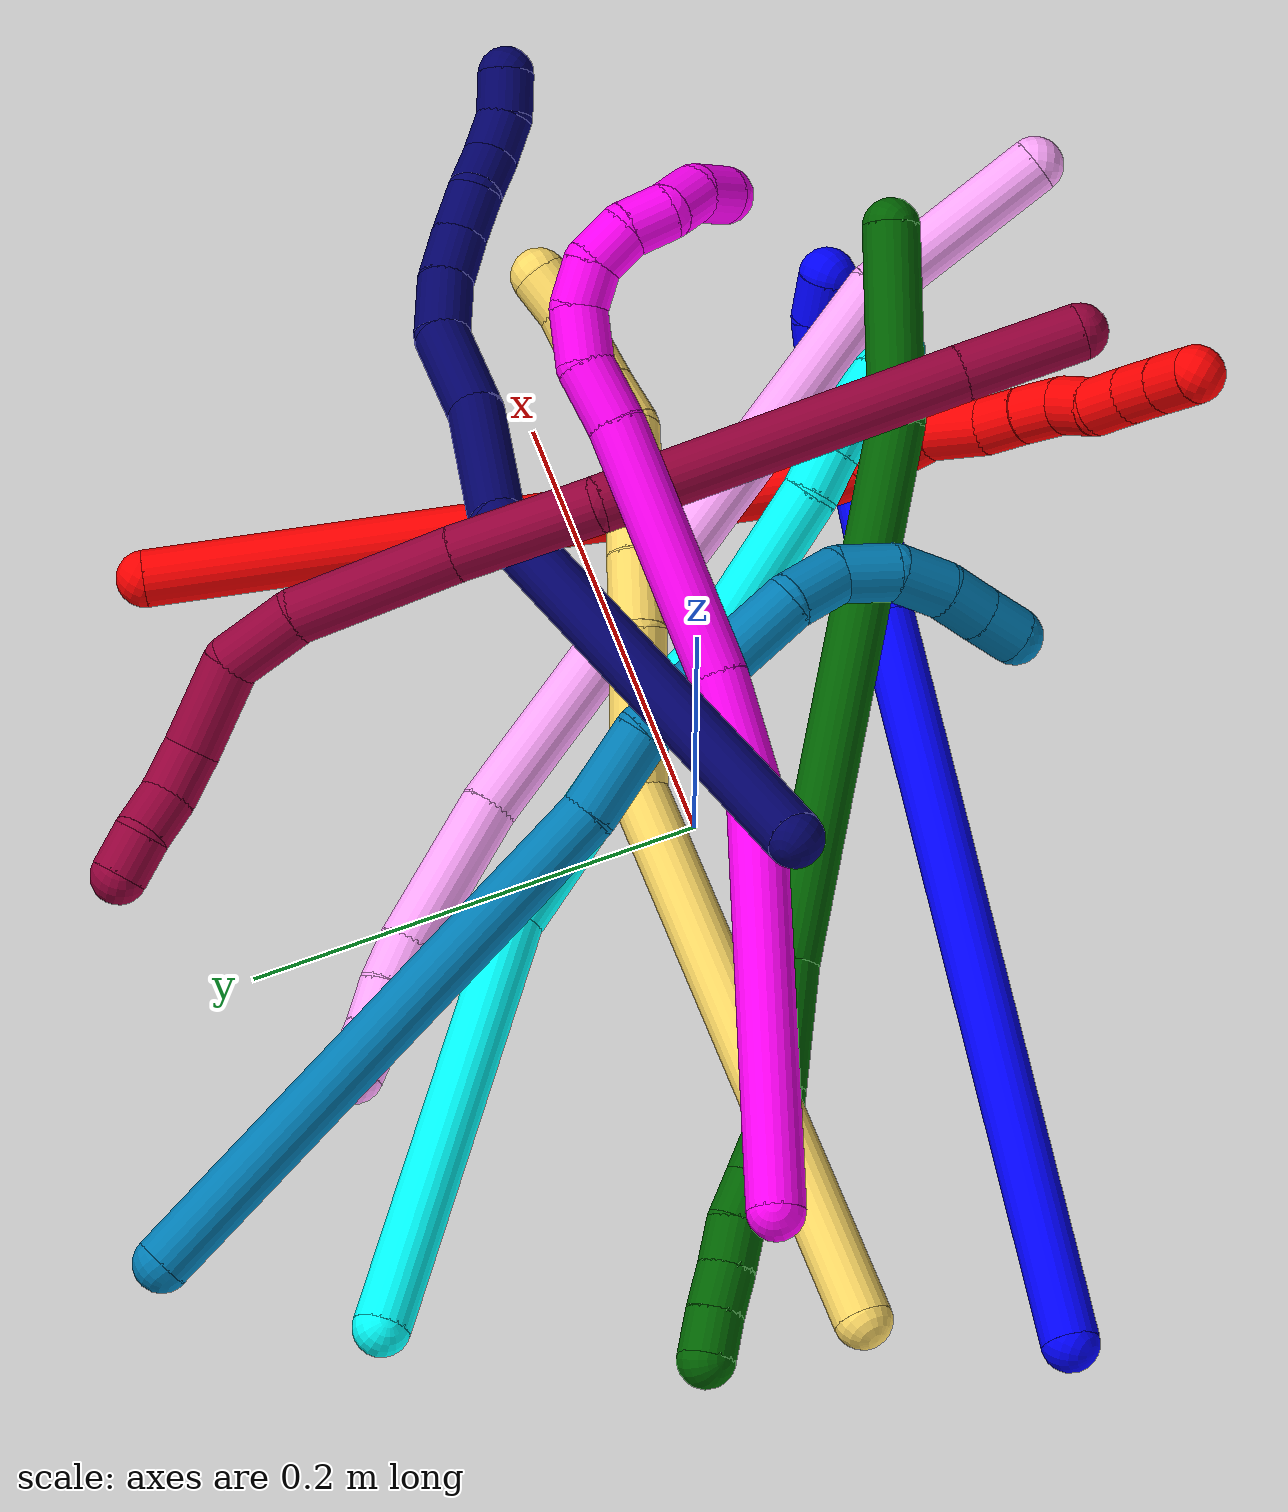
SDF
<sdf version="1.7">
 <world name="default">
  <plugin name="TubeGeneratorPlugin" filename="libtube_generator_plugin.so"/>
  <model name="photoneo_s_sensor">
   <static>1</static>
   <pose>0 0 2 1.57079 1.57079 3.14159</pose>
   <link name="link">
    <inertial><mass>0.1</mass></inertial>
    <sensor name="sensor" type="depth">
     <update_rate>30</update_rate>
     <camera>
      <horizontal_fov>1.22</horizontal_fov>
      <image><width>1920</width><height>1200</height><format>B8G8R8</format></image>
      <clip><near>0.1</near><far>2</far></clip>
      <depth_camera><output>points</output></depth_camera>
     </camera>
     <plugin name="camera_plugin" filename="libgazebo_ros_depth_camera.so">
      <baseline>0.2</baseline>
      <alwaysOn>1</alwaysOn>
      <updateRate>0.0</updateRate>
      <cameraName>camera_ir</cameraName>
      <imageTopicName>/camera/color/image_raw</imageTopicName>
      <cameraInfoTopicName>/camera/color/camera_info</cameraInfoTopicName>
      <depthImageTopicName>/camera/depth/image_raw</depthImageTopicName>
      <depthImageCameraInfoTopicName>/camera/depth/camera_info</depthImageCameraInfoTopicName>
      <pointCloudTopicName>/camera/depth/points</pointCloudTopicName>
      <frameName>fr_optical</frameName>
      <pointCloudCutoff>0.1</pointCloudCutoff>
      <pointCloudCutoffMax>2.0</pointCloudCutoffMax>
      <distortionK1>0</distortionK1>
      <distortionK2>0</distortionK2>
      <distortionK3>0</distortionK3>
      <distortionT1>0</distortionT1>
      <distortionT2>0</distortionT2>
      <CxPrime>0</CxPrime>
      <Cx>0</Cx>
      <Cy>0</Cy>
      <focalLength>0</focalLength>
      <hackBaseline>0</hackBaseline>
     </plugin>
    </sensor>
   </link>
  </model>
  <gravity>0 0 -9.8</gravity>
  <magnetic_field>6e-06 2.3e-05 -4.2e-05</magnetic_field>
  <atmosphere type="adiabatic"/>
  <physics name="default_physics" default="0" type="ode">
   <max_step_size>0.003</max_step_size>
   <real_time_factor>1</real_time_factor>
   <real_time_update_rate>1000</real_time_update_rate>
   <max_contacts>10000</max_contacts>
   <ode>
    <solver>
     <type>quick</type>
     <iters>100</iters>
     <sor>1.3</sor>
     <use_dynamic_moi_rescaling>0</use_dynamic_moi_rescaling>
    </solver>
    <constraints>
     <contact_max_correcting_vel>0</contact_max_correcting_vel>
     <contact_surface_layer>0.001</contact_surface_layer>
     <cfm>0</cfm>
     <erp>0.2</erp>
    </constraints>
   </ode>
  </physics>
  <scene><ambient>0.4 0.4 0.4 1</ambient><background>0.7 0.7 0.7 1</background><shadows>0</shadows></scene>
  <audio><device>default</device></audio>
  <spherical_coordinates>
   <surface_model>EARTH_WGS84</surface_model>
   <latitude_deg>0</latitude_deg>
   <longitude_deg>0</longitude_deg>
   <elevation>0</elevation>
   <heading_deg>0</heading_deg>
  </spherical_coordinates>
  <model name="bin">
   <static>1</static>
   <link name="bottom">
    <collision name="collision-bottom">
     <pose>0 0 -0.01 0 -0 0</pose>
     <geometry><box><size>0.8 0.6 0.02</size></box></geometry>
     <surface>
      <friction><ode><mu>100</mu><mu2>100</mu2></ode></friction>
      <contact><collide_bitmask>65535</collide_bitmask></contact>
     </surface>
    </collision>
   </link>
   <link name="west_wall">
    <collision name="collision-west_wall">
     <pose>-0.41 0 0.1 0 -0 0</pose>
     <geometry><box><size>0.02 0.6 0.2</size></box></geometry>
     <surface>
      <friction><ode><mu>100</mu><mu2>100</mu2></ode></friction>
      <contact><collide_bitmask>65535</collide_bitmask></contact>
     </surface>
    </collision>
   </link>
   <link name="east_wall">
    <collision name="collision-east_wall">
     <pose>0.41 0 0.1 0 -0 0</pose>
     <geometry><box><size>0.02 0.6 0.2</size></box></geometry>
     <surface>
      <friction><ode><mu>100</mu><mu2>100</mu2></ode></friction>
      <contact><collide_bitmask>65535</collide_bitmask></contact>
     </surface>
    </collision>
   </link>
   <link name="south_wall">
    <collision name="collision-south_wall">
     <pose>0 -0.31 0.1 0 -0 0</pose>
     <geometry><box><size>0.8 0.02 0.2</size></box></geometry>
     <surface>
      <friction><ode><mu>100</mu><mu2>100</mu2></ode></friction>
      <contact><collide_bitmask>65535</collide_bitmask></contact>
     </surface>
    </collision>
   </link>
   <link name="north_wall">
    <collision name="collision-north_wall">
     <pose>0 0.31 0.1 0 -0 0</pose>
     <geometry><box><size>0.8 0.02 0.2</size></box></geometry>
     <surface>
      <friction><ode><mu>100</mu><mu2>100</mu2></ode></friction>
      <contact><collide_bitmask>65535</collide_bitmask></contact>
     </surface>
    </collision>
   </link>
  </model>
  <model name="1">
   <static>0</static>
   <link name="1">
    <collision name="collision-cylinder-e_1_1_4">
     <pose>0.119617 -0.007287 -0.118999 3.08044 0.787053 2.99451</pose>
     <geometry><cylinder><radius>0.0125</radius><length>0.337768</length></cylinder></geometry>
     <surface>
      <friction><ode><mu>1.16</mu><mu2>1.16</mu2><slip1>0</slip1><slip2>0</slip2></ode></friction>
      <contact><ode><kp>1e+06</kp><kd>1</kd><max_vel>0</max_vel><min_depth>0.001</min_depth></ode></contact>
     </surface>
    </collision>
    <visual name="visual-cylinder-e_1_1_4">
     <pose>0.119617 -0.007287 -0.118999 3.08044 0.787053 2.99451</pose>
     <geometry><cylinder><radius>0.0125</radius><length>0.337768</length></cylinder></geometry>
     <material><ambient>0 0 1 1</ambient></material>
    </visual>
    <collision name="collision-cylinder-e_2_4_5">
     <pose>0.248944 -0.015117 -0.245702 3.0712 0.89888 2.99587</pose>
     <geometry><cylinder><radius>0.0125</radius><length>0.024815</length></cylinder></geometry>
     <surface>
      <friction><ode><mu>1.16</mu><mu2>1.16</mu2><slip1>0</slip1><slip2>0</slip2></ode></friction>
      <contact><ode><kp>1e+06</kp><kd>1</kd><max_vel>0</max_vel><min_depth>0.001</min_depth></ode></contact>
     </surface>
    </collision>
    <visual name="visual-cylinder-e_2_4_5">
     <pose>0.248944 -0.015117 -0.245702 3.0712 0.89888 2.99587</pose>
     <geometry><cylinder><radius>0.0125</radius><length>0.024815</length></cylinder></geometry>
     <material><ambient>0 0 1 1</ambient></material>
    </visual>
    <collision name="collision-cylinder-e_3_5_6">
     <pose>0.274275 -0.017603 -0.268377 3.01249 0.802459 2.83919</pose>
     <geometry><cylinder><radius>0.0125</radius><length>0.043447</length></cylinder></geometry>
     <surface>
      <friction><ode><mu>1.16</mu><mu2>1.16</mu2><slip1>0</slip1><slip2>0</slip2></ode></friction>
      <contact><ode><kp>1e+06</kp><kd>1</kd><max_vel>0</max_vel><min_depth>0.001</min_depth></ode></contact>
     </surface>
    </collision>
    <visual name="visual-cylinder-e_3_5_6">
     <pose>0.274275 -0.017603 -0.268377 3.01249 0.802459 2.83919</pose>
     <geometry><cylinder><radius>0.0125</radius><length>0.043447</length></cylinder></geometry>
     <material><ambient>0 0 1 1</ambient></material>
    </visual>
    <collision name="collision-cylinder-e_4_6_7">
     <pose>0.301347 -0.017378 -0.291222 -2.87275 0.951244 -2.62806</pose>
     <geometry><cylinder><radius>0.0125</radius><length>0.02813</length></cylinder></geometry>
     <surface>
      <friction><ode><mu>1.16</mu><mu2>1.16</mu2><slip1>0</slip1><slip2>0</slip2></ode></friction>
      <contact><ode><kp>1e+06</kp><kd>1</kd><max_vel>0</max_vel><min_depth>0.001</min_depth></ode></contact>
     </surface>
    </collision>
    <visual name="visual-cylinder-e_4_6_7">
     <pose>0.301347 -0.017378 -0.291222 -2.87275 0.951244 -2.62806</pose>
     <geometry><cylinder><radius>0.0125</radius><length>0.02813</length></cylinder></geometry>
     <material><ambient>0 0 1 1</ambient></material>
    </visual>
    <collision name="collision-cylinder-e_5_7_8">
     <pose>0.320934 -0.009474 -0.30644 -2.47866 0.717814 -1.65692</pose>
     <geometry><cylinder><radius>0.0125</radius><length>0.024741</length></cylinder></geometry>
     <surface>
      <friction><ode><mu>1.16</mu><mu2>1.16</mu2><slip1>0</slip1><slip2>0</slip2></ode></friction>
      <contact><ode><kp>1e+06</kp><kd>1</kd><max_vel>0</max_vel><min_depth>0.001</min_depth></ode></contact>
     </surface>
    </collision>
    <visual name="visual-cylinder-e_5_7_8">
     <pose>0.320934 -0.009474 -0.30644 -2.47866 0.717814 -1.65692</pose>
     <geometry><cylinder><radius>0.0125</radius><length>0.024741</length></cylinder></geometry>
     <material><ambient>0 0 1 1</ambient></material>
    </visual>
    <collision name="collision-cylinder-e_6_8_9">
     <pose>0.33757 0.001112 -0.316525 -2.08498 0.990472 -1.4934</pose>
     <geometry><cylinder><radius>0.0125</radius><length>0.020326</length></cylinder></geometry>
     <surface>
      <friction><ode><mu>1.16</mu><mu2>1.16</mu2><slip1>0</slip1><slip2>0</slip2></ode></friction>
      <contact><ode><kp>1e+06</kp><kd>1</kd><max_vel>0</max_vel><min_depth>0.001</min_depth></ode></contact>
     </surface>
    </collision>
    <visual name="visual-cylinder-e_6_8_9">
     <pose>0.33757 0.001112 -0.316525 -2.08498 0.990472 -1.4934</pose>
     <geometry><cylinder><radius>0.0125</radius><length>0.020326</length></cylinder></geometry>
     <material><ambient>0 0 1 1</ambient></material>
    </visual>
    <collision name="collision-cylinder-e_7_9_2">
     <pose>0.355215 0.010812 -0.318416 -1.39741 1.07712 -0.930368</pose>
     <geometry><cylinder><radius>0.0125</radius><length>0.020773</length></cylinder></geometry>
     <surface>
      <friction><ode><mu>1.16</mu><mu2>1.16</mu2><slip1>0</slip1><slip2>0</slip2></ode></friction>
      <contact><ode><kp>1e+06</kp><kd>1</kd><max_vel>0</max_vel><min_depth>0.001</min_depth></ode></contact>
     </surface>
    </collision>
    <visual name="visual-cylinder-e_7_9_2">
     <pose>0.355215 0.010812 -0.318416 -1.39741 1.07712 -0.930368</pose>
     <geometry><cylinder><radius>0.0125</radius><length>0.020773</length></cylinder></geometry>
     <material><ambient>0 0 1 1</ambient></material>
    </visual>
    <collision name="collision-sphere-2">
     <pose>0.364361 0.01566 -0.317567 0 -0 0</pose>
     <geometry><sphere><radius>0.0125</radius></sphere></geometry>
     <surface>
      <friction><ode><mu>1.16</mu><mu2>1.16</mu2><slip1>0</slip1><slip2>0</slip2></ode></friction>
      <contact><ode><kp>1e+06</kp><kd>1</kd><max_vel>0</max_vel><min_depth>0.001</min_depth></ode></contact>
     </surface>
    </collision>
    <visual name="visual-sphere-2">
     <pose>0.364361 0.01566 -0.317567 0 -0 0</pose>
     <geometry><sphere><radius>0.0125</radius></sphere></geometry>
     <material><ambient>0 0 1 1</ambient></material>
    </visual>
    <collision name="collision-sphere-9">
     <pose>0.346069 0.005964 -0.319265 0 -0 0</pose>
     <geometry><sphere><radius>0.0125</radius></sphere></geometry>
     <surface>
      <friction><ode><mu>1.16</mu><mu2>1.16</mu2><slip1>0</slip1><slip2>0</slip2></ode></friction>
      <contact><ode><kp>1e+06</kp><kd>1</kd><max_vel>0</max_vel><min_depth>0.001</min_depth></ode></contact>
     </surface>
    </collision>
    <visual name="visual-sphere-9">
     <pose>0.346069 0.005964 -0.319265 0 -0 0</pose>
     <geometry><sphere><radius>0.0125</radius></sphere></geometry>
     <material><ambient>0 0 1 1</ambient></material>
    </visual>
    <collision name="collision-sphere-4">
     <pose>0.239233 -0.014573 -0.237997 0 -0 0</pose>
     <geometry><sphere><radius>0.0125</radius></sphere></geometry>
     <surface>
      <friction><ode><mu>1.16</mu><mu2>1.16</mu2><slip1>0</slip1><slip2>0</slip2></ode></friction>
      <contact><ode><kp>1e+06</kp><kd>1</kd><max_vel>0</max_vel><min_depth>0.001</min_depth></ode></contact>
     </surface>
    </collision>
    <visual name="visual-sphere-4">
     <pose>0.239233 -0.014573 -0.237997 0 -0 0</pose>
     <geometry><sphere><radius>0.0125</radius></sphere></geometry>
     <material><ambient>0 0 1 1</ambient></material>
    </visual>
    <collision name="collision-sphere-1">
     <geometry><sphere><radius>0.0125</radius></sphere></geometry>
     <surface>
      <friction><ode><mu>1.16</mu><mu2>1.16</mu2><slip1>0</slip1><slip2>0</slip2></ode></friction>
      <contact><ode><kp>1e+06</kp><kd>1</kd><max_vel>0</max_vel><min_depth>0.001</min_depth></ode></contact>
     </surface>
    </collision>
    <visual name="visual-sphere-1">
     <geometry><sphere><radius>0.0125</radius></sphere></geometry>
     <material><ambient>0 0 1 1</ambient></material>
    </visual>
    <collision name="collision-sphere-8">
     <pose>0.329071 -0.003739 -0.313784 0 -0 0</pose>
     <geometry><sphere><radius>0.0125</radius></sphere></geometry>
     <surface>
      <friction><ode><mu>1.16</mu><mu2>1.16</mu2><slip1>0</slip1><slip2>0</slip2></ode></friction>
      <contact><ode><kp>1e+06</kp><kd>1</kd><max_vel>0</max_vel><min_depth>0.001</min_depth></ode></contact>
     </surface>
    </collision>
    <visual name="visual-sphere-8">
     <pose>0.329071 -0.003739 -0.313784 0 -0 0</pose>
     <geometry><sphere><radius>0.0125</radius></sphere></geometry>
     <material><ambient>0 0 1 1</ambient></material>
    </visual>
    <collision name="collision-sphere-5">
     <pose>0.258654 -0.01566 -0.253406 0 -0 0</pose>
     <geometry><sphere><radius>0.0125</radius></sphere></geometry>
     <surface>
      <friction><ode><mu>1.16</mu><mu2>1.16</mu2><slip1>0</slip1><slip2>0</slip2></ode></friction>
      <contact><ode><kp>1e+06</kp><kd>1</kd><max_vel>0</max_vel><min_depth>0.001</min_depth></ode></contact>
     </surface>
    </collision>
    <visual name="visual-sphere-5">
     <pose>0.258654 -0.01566 -0.253406 0 -0 0</pose>
     <geometry><sphere><radius>0.0125</radius></sphere></geometry>
     <material><ambient>0 0 1 1</ambient></material>
    </visual>
    <collision name="collision-sphere-6">
     <pose>0.289896 -0.019547 -0.283348 0 -0 0</pose>
     <geometry><sphere><radius>0.0125</radius></sphere></geometry>
     <surface>
      <friction><ode><mu>1.16</mu><mu2>1.16</mu2><slip1>0</slip1><slip2>0</slip2></ode></friction>
      <contact><ode><kp>1e+06</kp><kd>1</kd><max_vel>0</max_vel><min_depth>0.001</min_depth></ode></contact>
     </surface>
    </collision>
    <visual name="visual-sphere-6">
     <pose>0.289896 -0.019547 -0.283348 0 -0 0</pose>
     <geometry><sphere><radius>0.0125</radius></sphere></geometry>
     <material><ambient>0 0 1 1</ambient></material>
    </visual>
    <collision name="collision-sphere-7">
     <pose>0.312797 -0.015208 -0.299095 0 -0 0</pose>
     <geometry><sphere><radius>0.0125</radius></sphere></geometry>
     <surface>
      <friction><ode><mu>1.16</mu><mu2>1.16</mu2><slip1>0</slip1><slip2>0</slip2></ode></friction>
      <contact><ode><kp>1e+06</kp><kd>1</kd><max_vel>0</max_vel><min_depth>0.001</min_depth></ode></contact>
     </surface>
    </collision>
    <visual name="visual-sphere-7">
     <pose>0.312797 -0.015208 -0.299095 0 -0 0</pose>
     <geometry><sphere><radius>0.0125</radius></sphere></geometry>
     <material><ambient>0 0 1 1</ambient></material>
    </visual>
    <inertial>
     <pose>0.178308 -0.008154 -0.173546 0 -0 0</pose>
     <mass>0.5</mass>
     <inertia>
      <ixx>-0.0019</ixx>
      <ixy>0</ixy>
      <ixz>0</ixz>
      <iyy>0.003554</iyy>
      <iyz>0</iyz>
      <izz>-0.002186</izz>
     </inertia>
    </inertial>
   </link>
   <pose>-0.276237 -0.062437 0.013307 1.13841 -0.434693 -0.812801</pose>
  </model>
  <model name="2">
   <static>0</static>
   <link name="2">
    <collision name="collision-cylinder-e_1_1_4">
     <pose>0.016531 -0.086992 -0.117207 2.5031 0.112778 0.338277</pose>
     <geometry><cylinder><radius>0.0125</radius><length>0.29379</length></cylinder></geometry>
     <surface>
      <friction><ode><mu>1.16</mu><mu2>1.16</mu2><slip1>0</slip1><slip2>0</slip2></ode></friction>
      <contact><ode><kp>1e+06</kp><kd>1</kd><max_vel>0</max_vel><min_depth>0.001</min_depth></ode></contact>
     </surface>
    </collision>
    <visual name="visual-cylinder-e_1_1_4">
     <pose>0.016531 -0.086992 -0.117207 2.5031 0.112778 0.338277</pose>
     <geometry><cylinder><radius>0.0125</radius><length>0.29379</length></cylinder></geometry>
     <material><ambient>1 0 0 1</ambient></material>
    </visual>
    <collision name="collision-cylinder-e_2_4_5">
     <pose>0.032772 -0.181449 -0.241254 2.31257 -0.028709 -0.065229</pose>
     <geometry><cylinder><radius>0.0125</radius><length>0.02026</length></cylinder></geometry>
     <surface>
      <friction><ode><mu>1.16</mu><mu2>1.16</mu2><slip1>0</slip1><slip2>0</slip2></ode></friction>
      <contact><ode><kp>1e+06</kp><kd>1</kd><max_vel>0</max_vel><min_depth>0.001</min_depth></ode></contact>
     </surface>
    </collision>
    <visual name="visual-cylinder-e_2_4_5">
     <pose>0.032772 -0.181449 -0.241254 2.31257 -0.028709 -0.065229</pose>
     <geometry><cylinder><radius>0.0125</radius><length>0.02026</length></cylinder></geometry>
     <material><ambient>1 0 0 1</ambient></material>
    </visual>
    <collision name="collision-cylinder-e_3_5_6">
     <pose>0.02345 -0.20289 -0.257767 2.17615 -0.488439 -0.887697</pose>
     <geometry><cylinder><radius>0.0125</radius><length>0.038493</length></cylinder></geometry>
     <surface>
      <friction><ode><mu>1.16</mu><mu2>1.16</mu2><slip1>0</slip1><slip2>0</slip2></ode></friction>
      <contact><ode><kp>1e+06</kp><kd>1</kd><max_vel>0</max_vel><min_depth>0.001</min_depth></ode></contact>
     </surface>
    </collision>
    <visual name="visual-cylinder-e_3_5_6">
     <pose>0.02345 -0.20289 -0.257767 2.17615 -0.488439 -0.887697</pose>
     <geometry><cylinder><radius>0.0125</radius><length>0.038493</length></cylinder></geometry>
     <material><ambient>1 0 0 1</ambient></material>
    </visual>
    <collision name="collision-cylinder-e_4_6_7">
     <pose>0.010991 -0.223986 -0.277875 2.54293 -0.264944 -0.81522</pose>
     <geometry><cylinder><radius>0.0125</radius><length>0.026182</length></cylinder></geometry>
     <surface>
      <friction><ode><mu>1.16</mu><mu2>1.16</mu2><slip1>0</slip1><slip2>0</slip2></ode></friction>
      <contact><ode><kp>1e+06</kp><kd>1</kd><max_vel>0</max_vel><min_depth>0.001</min_depth></ode></contact>
     </surface>
    </collision>
    <visual name="visual-cylinder-e_4_6_7">
     <pose>0.010991 -0.223986 -0.277875 2.54293 -0.264944 -0.81522</pose>
     <geometry><cylinder><radius>0.0125</radius><length>0.026182</length></cylinder></geometry>
     <material><ambient>1 0 0 1</ambient></material>
    </visual>
    <collision name="collision-cylinder-e_5_7_8">
     <pose>0.002363 -0.237255 -0.294557 2.36388 -0.535504 -1.18004</pose>
     <geometry><cylinder><radius>0.0125</radius><length>0.020382</length></cylinder></geometry>
     <surface>
      <friction><ode><mu>1.16</mu><mu2>1.16</mu2><slip1>0</slip1><slip2>0</slip2></ode></friction>
      <contact><ode><kp>1e+06</kp><kd>1</kd><max_vel>0</max_vel><min_depth>0.001</min_depth></ode></contact>
     </surface>
    </collision>
    <visual name="visual-cylinder-e_5_7_8">
     <pose>0.002363 -0.237255 -0.294557 2.36388 -0.535504 -1.18004</pose>
     <geometry><cylinder><radius>0.0125</radius><length>0.020382</length></cylinder></geometry>
     <material><ambient>1 0 0 1</ambient></material>
    </visual>
    <collision name="collision-cylinder-e_6_8_9">
     <pose>-0.007592 -0.249417 -0.307336 2.39769 -0.491571 -1.14294</pose>
     <geometry><cylinder><radius>0.0125</radius><length>0.020145</length></cylinder></geometry>
     <surface>
      <friction><ode><mu>1.16</mu><mu2>1.16</mu2><slip1>0</slip1><slip2>0</slip2></ode></friction>
      <contact><ode><kp>1e+06</kp><kd>1</kd><max_vel>0</max_vel><min_depth>0.001</min_depth></ode></contact>
     </surface>
    </collision>
    <visual name="visual-cylinder-e_6_8_9">
     <pose>-0.007592 -0.249417 -0.307336 2.39769 -0.491571 -1.14294</pose>
     <geometry><cylinder><radius>0.0125</radius><length>0.020145</length></cylinder></geometry>
     <material><ambient>1 0 0 1</ambient></material>
    </visual>
    <collision name="collision-cylinder-e_7_9_10">
     <pose>-0.019617 -0.258591 -0.320346 2.68759 -0.789853 -2.12955</pose>
     <geometry><cylinder><radius>0.0125</radius><length>0.020473</length></cylinder></geometry>
     <surface>
      <friction><ode><mu>1.16</mu><mu2>1.16</mu2><slip1>0</slip1><slip2>0</slip2></ode></friction>
      <contact><ode><kp>1e+06</kp><kd>1</kd><max_vel>0</max_vel><min_depth>0.001</min_depth></ode></contact>
     </surface>
    </collision>
    <visual name="visual-cylinder-e_7_9_10">
     <pose>-0.019617 -0.258591 -0.320346 2.68759 -0.789853 -2.12955</pose>
     <geometry><cylinder><radius>0.0125</radius><length>0.020473</length></cylinder></geometry>
     <material><ambient>1 0 0 1</ambient></material>
    </visual>
    <collision name="collision-cylinder-e_8_10_11">
     <pose>-0.032578 -0.267865 -0.332462 2.31593 -0.599965 -1.22975</pose>
     <geometry><cylinder><radius>0.0125</radius><length>0.020158</length></cylinder></geometry>
     <surface>
      <friction><ode><mu>1.16</mu><mu2>1.16</mu2><slip1>0</slip1><slip2>0</slip2></ode></friction>
      <contact><ode><kp>1e+06</kp><kd>1</kd><max_vel>0</max_vel><min_depth>0.001</min_depth></ode></contact>
     </surface>
    </collision>
    <visual name="visual-cylinder-e_8_10_11">
     <pose>-0.032578 -0.267865 -0.332462 2.31593 -0.599965 -1.22975</pose>
     <geometry><cylinder><radius>0.0125</radius><length>0.020158</length></cylinder></geometry>
     <material><ambient>1 0 0 1</ambient></material>
    </visual>
    <collision name="collision-cylinder-e_9_11_12">
     <pose>-0.044854 -0.279359 -0.343382 2.34667 -0.718113 -1.45903</pose>
     <geometry><cylinder><radius>0.0125</radius><length>0.020017</length></cylinder></geometry>
     <surface>
      <friction><ode><mu>1.16</mu><mu2>1.16</mu2><slip1>0</slip1><slip2>0</slip2></ode></friction>
      <contact><ode><kp>1e+06</kp><kd>1</kd><max_vel>0</max_vel><min_depth>0.001</min_depth></ode></contact>
     </surface>
    </collision>
    <visual name="visual-cylinder-e_9_11_12">
     <pose>-0.044854 -0.279359 -0.343382 2.34667 -0.718113 -1.45903</pose>
     <geometry><cylinder><radius>0.0125</radius><length>0.020017</length></cylinder></geometry>
     <material><ambient>1 0 0 1</ambient></material>
    </visual>
    <collision name="collision-cylinder-e_10_12_2">
     <pose>-0.058253 -0.289972 -0.353875 2.35446 -0.744979 -1.51001</pose>
     <geometry><cylinder><radius>0.0125</radius><length>0.0201</length></cylinder></geometry>
     <surface>
      <friction><ode><mu>1.16</mu><mu2>1.16</mu2><slip1>0</slip1><slip2>0</slip2></ode></friction>
      <contact><ode><kp>1e+06</kp><kd>1</kd><max_vel>0</max_vel><min_depth>0.001</min_depth></ode></contact>
     </surface>
    </collision>
    <visual name="visual-cylinder-e_10_12_2">
     <pose>-0.058253 -0.289972 -0.353875 2.35446 -0.744979 -1.51001</pose>
     <geometry><cylinder><radius>0.0125</radius><length>0.0201</length></cylinder></geometry>
     <material><ambient>1 0 0 1</ambient></material>
    </visual>
    <collision name="collision-sphere-2">
     <pose>-0.065066 -0.295205 -0.35909 0 -0 0</pose>
     <geometry><sphere><radius>0.0125</radius></sphere></geometry>
     <surface>
      <friction><ode><mu>1.16</mu><mu2>1.16</mu2><slip1>0</slip1><slip2>0</slip2></ode></friction>
      <contact><ode><kp>1e+06</kp><kd>1</kd><max_vel>0</max_vel><min_depth>0.001</min_depth></ode></contact>
     </surface>
    </collision>
    <visual name="visual-sphere-2">
     <pose>-0.065066 -0.295205 -0.35909 0 -0 0</pose>
     <geometry><sphere><radius>0.0125</radius></sphere></geometry>
     <material><ambient>1 0 0 1</ambient></material>
    </visual>
    <collision name="collision-sphere-12">
     <pose>-0.051439 -0.284739 -0.34866 0 -0 0</pose>
     <geometry><sphere><radius>0.0125</radius></sphere></geometry>
     <surface>
      <friction><ode><mu>1.16</mu><mu2>1.16</mu2><slip1>0</slip1><slip2>0</slip2></ode></friction>
      <contact><ode><kp>1e+06</kp><kd>1</kd><max_vel>0</max_vel><min_depth>0.001</min_depth></ode></contact>
     </surface>
    </collision>
    <visual name="visual-sphere-12">
     <pose>-0.051439 -0.284739 -0.34866 0 -0 0</pose>
     <geometry><sphere><radius>0.0125</radius></sphere></geometry>
     <material><ambient>1 0 0 1</ambient></material>
    </visual>
    <collision name="collision-sphere-11">
     <pose>-0.038269 -0.273979 -0.338103 0 -0 0</pose>
     <geometry><sphere><radius>0.0125</radius></sphere></geometry>
     <surface>
      <friction><ode><mu>1.16</mu><mu2>1.16</mu2><slip1>0</slip1><slip2>0</slip2></ode></friction>
      <contact><ode><kp>1e+06</kp><kd>1</kd><max_vel>0</max_vel><min_depth>0.001</min_depth></ode></contact>
     </surface>
    </collision>
    <visual name="visual-sphere-11">
     <pose>-0.038269 -0.273979 -0.338103 0 -0 0</pose>
     <geometry><sphere><radius>0.0125</radius></sphere></geometry>
     <material><ambient>1 0 0 1</ambient></material>
    </visual>
    <collision name="collision-sphere-10">
     <pose>-0.026887 -0.261751 -0.326822 0 -0 0</pose>
     <geometry><sphere><radius>0.0125</radius></sphere></geometry>
     <surface>
      <friction><ode><mu>1.16</mu><mu2>1.16</mu2><slip1>0</slip1><slip2>0</slip2></ode></friction>
      <contact><ode><kp>1e+06</kp><kd>1</kd><max_vel>0</max_vel><min_depth>0.001</min_depth></ode></contact>
     </surface>
    </collision>
    <visual name="visual-sphere-10">
     <pose>-0.026887 -0.261751 -0.326822 0 -0 0</pose>
     <geometry><sphere><radius>0.0125</radius></sphere></geometry>
     <material><ambient>1 0 0 1</ambient></material>
    </visual>
    <collision name="collision-sphere-9">
     <pose>-0.012346 -0.25543 -0.31387 0 -0 0</pose>
     <geometry><sphere><radius>0.0125</radius></sphere></geometry>
     <surface>
      <friction><ode><mu>1.16</mu><mu2>1.16</mu2><slip1>0</slip1><slip2>0</slip2></ode></friction>
      <contact><ode><kp>1e+06</kp><kd>1</kd><max_vel>0</max_vel><min_depth>0.001</min_depth></ode></contact>
     </surface>
    </collision>
    <visual name="visual-sphere-9">
     <pose>-0.012346 -0.25543 -0.31387 0 -0 0</pose>
     <geometry><sphere><radius>0.0125</radius></sphere></geometry>
     <material><ambient>1 0 0 1</ambient></material>
    </visual>
    <collision name="collision-sphere-4">
     <pose>0.033063 -0.173983 -0.234413 0 -0 0</pose>
     <geometry><sphere><radius>0.0125</radius></sphere></geometry>
     <surface>
      <friction><ode><mu>1.16</mu><mu2>1.16</mu2><slip1>0</slip1><slip2>0</slip2></ode></friction>
      <contact><ode><kp>1e+06</kp><kd>1</kd><max_vel>0</max_vel><min_depth>0.001</min_depth></ode></contact>
     </surface>
    </collision>
    <visual name="visual-sphere-4">
     <pose>0.033063 -0.173983 -0.234413 0 -0 0</pose>
     <geometry><sphere><radius>0.0125</radius></sphere></geometry>
     <material><ambient>1 0 0 1</ambient></material>
    </visual>
    <collision name="collision-sphere-1">
     <geometry><sphere><radius>0.0125</radius></sphere></geometry>
     <surface>
      <friction><ode><mu>1.16</mu><mu2>1.16</mu2><slip1>0</slip1><slip2>0</slip2></ode></friction>
      <contact><ode><kp>1e+06</kp><kd>1</kd><max_vel>0</max_vel><min_depth>0.001</min_depth></ode></contact>
     </surface>
    </collision>
    <visual name="visual-sphere-1">
     <geometry><sphere><radius>0.0125</radius></sphere></geometry>
     <material><ambient>1 0 0 1</ambient></material>
    </visual>
    <collision name="collision-sphere-8">
     <pose>-0.002838 -0.243404 -0.300802 0 -0 0</pose>
     <geometry><sphere><radius>0.0125</radius></sphere></geometry>
     <surface>
      <friction><ode><mu>1.16</mu><mu2>1.16</mu2><slip1>0</slip1><slip2>0</slip2></ode></friction>
      <contact><ode><kp>1e+06</kp><kd>1</kd><max_vel>0</max_vel><min_depth>0.001</min_depth></ode></contact>
     </surface>
    </collision>
    <visual name="visual-sphere-8">
     <pose>-0.002838 -0.243404 -0.300802 0 -0 0</pose>
     <geometry><sphere><radius>0.0125</radius></sphere></geometry>
     <material><ambient>1 0 0 1</ambient></material>
    </visual>
    <collision name="collision-sphere-5">
     <pose>0.032481 -0.188914 -0.248095 0 -0 0</pose>
     <geometry><sphere><radius>0.0125</radius></sphere></geometry>
     <surface>
      <friction><ode><mu>1.16</mu><mu2>1.16</mu2><slip1>0</slip1><slip2>0</slip2></ode></friction>
      <contact><ode><kp>1e+06</kp><kd>1</kd><max_vel>0</max_vel><min_depth>0.001</min_depth></ode></contact>
     </surface>
    </collision>
    <visual name="visual-sphere-5">
     <pose>0.032481 -0.188914 -0.248095 0 -0 0</pose>
     <geometry><sphere><radius>0.0125</radius></sphere></geometry>
     <material><ambient>1 0 0 1</ambient></material>
    </visual>
    <collision name="collision-sphere-6">
     <pose>0.014418 -0.216866 -0.267438 0 -0 0</pose>
     <geometry><sphere><radius>0.0125</radius></sphere></geometry>
     <surface>
      <friction><ode><mu>1.16</mu><mu2>1.16</mu2><slip1>0</slip1><slip2>0</slip2></ode></friction>
      <contact><ode><kp>1e+06</kp><kd>1</kd><max_vel>0</max_vel><min_depth>0.001</min_depth></ode></contact>
     </surface>
    </collision>
    <visual name="visual-sphere-6">
     <pose>0.014418 -0.216866 -0.267438 0 -0 0</pose>
     <geometry><sphere><radius>0.0125</radius></sphere></geometry>
     <material><ambient>1 0 0 1</ambient></material>
    </visual>
    <collision name="collision-sphere-7">
     <pose>0.007563 -0.231106 -0.288312 0 -0 0</pose>
     <geometry><sphere><radius>0.0125</radius></sphere></geometry>
     <surface>
      <friction><ode><mu>1.16</mu><mu2>1.16</mu2><slip1>0</slip1><slip2>0</slip2></ode></friction>
      <contact><ode><kp>1e+06</kp><kd>1</kd><max_vel>0</max_vel><min_depth>0.001</min_depth></ode></contact>
     </surface>
    </collision>
    <visual name="visual-sphere-7">
     <pose>0.007563 -0.231106 -0.288312 0 -0 0</pose>
     <geometry><sphere><radius>0.0125</radius></sphere></geometry>
     <material><ambient>1 0 0 1</ambient></material>
    </visual>
    <inertial>
     <pose>0.006959 -0.149764 -0.191922 0 -0 0</pose>
     <mass>0.5</mass>
     <inertia>
      <ixx>0.002682</ixx>
      <ixy>0</ixy>
      <ixz>0</ixz>
      <iyy>-0.000897</iyy>
      <iyz>0</iyz>
      <izz>0.001012</izz>
     </inertia>
    </inertial>
   </link>
   <pose>0.187479 0.183368 0.012682 -1.30063 1.09919 -0.609195</pose>
  </model>
  <model name="3">
   <static>0</static>
   <link name="3">
    <collision name="collision-cylinder-e_1_1_4">
     <pose>0.069147 -0.066506 0.002081 1.53951 0.804624 0.782323</pose>
     <geometry><cylinder><radius>0.0125</radius><length>0.191923</length></cylinder></geometry>
     <surface>
      <friction><ode><mu>1.16</mu><mu2>1.16</mu2><slip1>0</slip1><slip2>0</slip2></ode></friction>
      <contact><ode><kp>1e+06</kp><kd>1</kd><max_vel>0</max_vel><min_depth>0.001</min_depth></ode></contact>
     </surface>
    </collision>
    <visual name="visual-cylinder-e_1_1_4">
     <pose>0.069147 -0.066506 0.002081 1.53951 0.804624 0.782323</pose>
     <geometry><cylinder><radius>0.0125</radius><length>0.191923</length></cylinder></geometry>
     <material><ambient>0.003922 1 0.996078 1</ambient></material>
    </visual>
    <collision name="collision-cylinder-e_2_4_5">
     <pose>0.167105 -0.1803 0.016339 1.31878 0.533033 0.417084</pose>
     <geometry><cylinder><radius>0.0125</radius><length>0.113394</length></cylinder></geometry>
     <surface>
      <friction><ode><mu>1.16</mu><mu2>1.16</mu2><slip1>0</slip1><slip2>0</slip2></ode></friction>
      <contact><ode><kp>1e+06</kp><kd>1</kd><max_vel>0</max_vel><min_depth>0.001</min_depth></ode></contact>
     </surface>
    </collision>
    <visual name="visual-cylinder-e_2_4_5">
     <pose>0.167105 -0.1803 0.016339 1.31878 0.533033 0.417084</pose>
     <geometry><cylinder><radius>0.0125</radius><length>0.113394</length></cylinder></geometry>
     <material><ambient>0.003922 1 0.996078 1</ambient></material>
    </visual>
    <collision name="collision-cylinder-e_3_5_6">
     <pose>0.201566 -0.240008 0.029186 1.51688 0.426453 0.404681</pose>
     <geometry><cylinder><radius>0.0125</radius><length>0.027321</length></cylinder></geometry>
     <surface>
      <friction><ode><mu>1.16</mu><mu2>1.16</mu2><slip1>0</slip1><slip2>0</slip2></ode></friction>
      <contact><ode><kp>1e+06</kp><kd>1</kd><max_vel>0</max_vel><min_depth>0.001</min_depth></ode></contact>
     </surface>
    </collision>
    <visual name="visual-cylinder-e_3_5_6">
     <pose>0.201566 -0.240008 0.029186 1.51688 0.426453 0.404681</pose>
     <geometry><cylinder><radius>0.0125</radius><length>0.027321</length></cylinder></geometry>
     <material><ambient>0.003922 1 0.996078 1</ambient></material>
    </visual>
    <collision name="collision-cylinder-e_4_6_7">
     <pose>0.228046 -0.28359 0.051774 0.957841 0.500322 0.263805</pose>
     <geometry><cylinder><radius>0.0125</radius><length>0.086844</length></cylinder></geometry>
     <surface>
      <friction><ode><mu>1.16</mu><mu2>1.16</mu2><slip1>0</slip1><slip2>0</slip2></ode></friction>
      <contact><ode><kp>1e+06</kp><kd>1</kd><max_vel>0</max_vel><min_depth>0.001</min_depth></ode></contact>
     </surface>
    </collision>
    <visual name="visual-cylinder-e_4_6_7">
     <pose>0.228046 -0.28359 0.051774 0.957841 0.500322 0.263805</pose>
     <geometry><cylinder><radius>0.0125</radius><length>0.086844</length></cylinder></geometry>
     <material><ambient>0.003922 1 0.996078 1</ambient></material>
    </visual>
    <collision name="collision-cylinder-e_5_7_8">
     <pose>0.254917 -0.321879 0.077343 1.09728 0.646428 0.403895</pose>
     <geometry><cylinder><radius>0.0125</radius><length>0.020057</length></cylinder></geometry>
     <surface>
      <friction><ode><mu>1.16</mu><mu2>1.16</mu2><slip1>0</slip1><slip2>0</slip2></ode></friction>
      <contact><ode><kp>1e+06</kp><kd>1</kd><max_vel>0</max_vel><min_depth>0.001</min_depth></ode></contact>
     </surface>
    </collision>
    <visual name="visual-cylinder-e_5_7_8">
     <pose>0.254917 -0.321879 0.077343 1.09728 0.646428 0.403895</pose>
     <geometry><cylinder><radius>0.0125</radius><length>0.020057</length></cylinder></geometry>
     <material><ambient>0.003922 1 0.996078 1</ambient></material>
    </visual>
    <collision name="collision-cylinder-e_6_8_9">
     <pose>0.266626 -0.336652 0.08447 1.14423 0.593485 0.388829</pose>
     <geometry><cylinder><radius>0.0125</radius><length>0.020272</length></cylinder></geometry>
     <surface>
      <friction><ode><mu>1.16</mu><mu2>1.16</mu2><slip1>0</slip1><slip2>0</slip2></ode></friction>
      <contact><ode><kp>1e+06</kp><kd>1</kd><max_vel>0</max_vel><min_depth>0.001</min_depth></ode></contact>
     </surface>
    </collision>
    <visual name="visual-cylinder-e_6_8_9">
     <pose>0.266626 -0.336652 0.08447 1.14423 0.593485 0.388829</pose>
     <geometry><cylinder><radius>0.0125</radius><length>0.020272</length></cylinder></geometry>
     <material><ambient>0.003922 1 0.996078 1</ambient></material>
    </visual>
    <collision name="collision-cylinder-e_7_9_10">
     <pose>0.277519 -0.352863 0.087171 1.66113 0.546154 0.594982</pose>
     <geometry><cylinder><radius>0.0125</radius><length>0.020119</length></cylinder></geometry>
     <surface>
      <friction><ode><mu>1.16</mu><mu2>1.16</mu2><slip1>0</slip1><slip2>0</slip2></ode></friction>
      <contact><ode><kp>1e+06</kp><kd>1</kd><max_vel>0</max_vel><min_depth>0.001</min_depth></ode></contact>
     </surface>
    </collision>
    <visual name="visual-cylinder-e_7_9_10">
     <pose>0.277519 -0.352863 0.087171 1.66113 0.546154 0.594982</pose>
     <geometry><cylinder><radius>0.0125</radius><length>0.020119</length></cylinder></geometry>
     <material><ambient>0.003922 1 0.996078 1</ambient></material>
    </visual>
    <collision name="collision-cylinder-e_8_10_2">
     <pose>0.287693 -0.369965 0.084589 1.77932 0.515692 0.629114</pose>
     <geometry><cylinder><radius>0.0125</radius><length>0.02007</length></cylinder></geometry>
     <surface>
      <friction><ode><mu>1.16</mu><mu2>1.16</mu2><slip1>0</slip1><slip2>0</slip2></ode></friction>
      <contact><ode><kp>1e+06</kp><kd>1</kd><max_vel>0</max_vel><min_depth>0.001</min_depth></ode></contact>
     </surface>
    </collision>
    <visual name="visual-cylinder-e_8_10_2">
     <pose>0.287693 -0.369965 0.084589 1.77932 0.515692 0.629114</pose>
     <geometry><cylinder><radius>0.0125</radius><length>0.02007</length></cylinder></geometry>
     <material><ambient>0.003922 1 0.996078 1</ambient></material>
    </visual>
    <collision name="collision-sphere-2">
     <pose>0.292641 -0.378506 0.082781 0 -0 0</pose>
     <geometry><sphere><radius>0.0125</radius></sphere></geometry>
     <surface>
      <friction><ode><mu>1.16</mu><mu2>1.16</mu2><slip1>0</slip1><slip2>0</slip2></ode></friction>
      <contact><ode><kp>1e+06</kp><kd>1</kd><max_vel>0</max_vel><min_depth>0.001</min_depth></ode></contact>
     </surface>
    </collision>
    <visual name="visual-sphere-2">
     <pose>0.292641 -0.378506 0.082781 0 -0 0</pose>
     <geometry><sphere><radius>0.0125</radius></sphere></geometry>
     <material><ambient>0.003922 1 0.996078 1</ambient></material>
    </visual>
    <collision name="collision-sphere-10">
     <pose>0.282744 -0.361424 0.086396 0 -0 0</pose>
     <geometry><sphere><radius>0.0125</radius></sphere></geometry>
     <surface>
      <friction><ode><mu>1.16</mu><mu2>1.16</mu2><slip1>0</slip1><slip2>0</slip2></ode></friction>
      <contact><ode><kp>1e+06</kp><kd>1</kd><max_vel>0</max_vel><min_depth>0.001</min_depth></ode></contact>
     </surface>
    </collision>
    <visual name="visual-sphere-10">
     <pose>0.282744 -0.361424 0.086396 0 -0 0</pose>
     <geometry><sphere><radius>0.0125</radius></sphere></geometry>
     <material><ambient>0.003922 1 0.996078 1</ambient></material>
    </visual>
    <collision name="collision-sphere-9">
     <pose>0.272294 -0.344302 0.087947 0 -0 0</pose>
     <geometry><sphere><radius>0.0125</radius></sphere></geometry>
     <surface>
      <friction><ode><mu>1.16</mu><mu2>1.16</mu2><slip1>0</slip1><slip2>0</slip2></ode></friction>
      <contact><ode><kp>1e+06</kp><kd>1</kd><max_vel>0</max_vel><min_depth>0.001</min_depth></ode></contact>
     </surface>
    </collision>
    <visual name="visual-sphere-9">
     <pose>0.272294 -0.344302 0.087947 0 -0 0</pose>
     <geometry><sphere><radius>0.0125</radius></sphere></geometry>
     <material><ambient>0.003922 1 0.996078 1</ambient></material>
    </visual>
    <collision name="collision-sphere-4">
     <pose>0.138294 -0.133011 0.004162 0 -0 0</pose>
     <geometry><sphere><radius>0.0125</radius></sphere></geometry>
     <surface>
      <friction><ode><mu>1.16</mu><mu2>1.16</mu2><slip1>0</slip1><slip2>0</slip2></ode></friction>
      <contact><ode><kp>1e+06</kp><kd>1</kd><max_vel>0</max_vel><min_depth>0.001</min_depth></ode></contact>
     </surface>
    </collision>
    <visual name="visual-sphere-4">
     <pose>0.138294 -0.133011 0.004162 0 -0 0</pose>
     <geometry><sphere><radius>0.0125</radius></sphere></geometry>
     <material><ambient>0.003922 1 0.996078 1</ambient></material>
    </visual>
    <collision name="collision-sphere-1">
     <geometry><sphere><radius>0.0125</radius></sphere></geometry>
     <surface>
      <friction><ode><mu>1.16</mu><mu2>1.16</mu2><slip1>0</slip1><slip2>0</slip2></ode></friction>
      <contact><ode><kp>1e+06</kp><kd>1</kd><max_vel>0</max_vel><min_depth>0.001</min_depth></ode></contact>
     </surface>
    </collision>
    <visual name="visual-sphere-1">
     <geometry><sphere><radius>0.0125</radius></sphere></geometry>
     <material><ambient>0.003922 1 0.996078 1</ambient></material>
    </visual>
    <collision name="collision-sphere-8">
     <pose>0.260957 -0.329003 0.080994 0 -0 0</pose>
     <geometry><sphere><radius>0.0125</radius></sphere></geometry>
     <surface>
      <friction><ode><mu>1.16</mu><mu2>1.16</mu2><slip1>0</slip1><slip2>0</slip2></ode></friction>
      <contact><ode><kp>1e+06</kp><kd>1</kd><max_vel>0</max_vel><min_depth>0.001</min_depth></ode></contact>
     </surface>
    </collision>
    <visual name="visual-sphere-8">
     <pose>0.260957 -0.329003 0.080994 0 -0 0</pose>
     <geometry><sphere><radius>0.0125</radius></sphere></geometry>
     <material><ambient>0.003922 1 0.996078 1</ambient></material>
    </visual>
    <collision name="collision-sphere-5">
     <pose>0.195915 -0.227589 0.028516 0 -0 0</pose>
     <geometry><sphere><radius>0.0125</radius></sphere></geometry>
     <surface>
      <friction><ode><mu>1.16</mu><mu2>1.16</mu2><slip1>0</slip1><slip2>0</slip2></ode></friction>
      <contact><ode><kp>1e+06</kp><kd>1</kd><max_vel>0</max_vel><min_depth>0.001</min_depth></ode></contact>
     </surface>
    </collision>
    <visual name="visual-sphere-5">
     <pose>0.195915 -0.227589 0.028516 0 -0 0</pose>
     <geometry><sphere><radius>0.0125</radius></sphere></geometry>
     <material><ambient>0.003922 1 0.996078 1</ambient></material>
    </visual>
    <collision name="collision-sphere-6">
     <pose>0.207216 -0.252427 0.029856 0 -0 0</pose>
     <geometry><sphere><radius>0.0125</radius></sphere></geometry>
     <surface>
      <friction><ode><mu>1.16</mu><mu2>1.16</mu2><slip1>0</slip1><slip2>0</slip2></ode></friction>
      <contact><ode><kp>1e+06</kp><kd>1</kd><max_vel>0</max_vel><min_depth>0.001</min_depth></ode></contact>
     </surface>
    </collision>
    <visual name="visual-sphere-6">
     <pose>0.207216 -0.252427 0.029856 0 -0 0</pose>
     <geometry><sphere><radius>0.0125</radius></sphere></geometry>
     <material><ambient>0.003922 1 0.996078 1</ambient></material>
    </visual>
    <collision name="collision-sphere-7">
     <pose>0.248876 -0.314754 0.073693 0 -0 0</pose>
     <geometry><sphere><radius>0.0125</radius></sphere></geometry>
     <surface>
      <friction><ode><mu>1.16</mu><mu2>1.16</mu2><slip1>0</slip1><slip2>0</slip2></ode></friction>
      <contact><ode><kp>1e+06</kp><kd>1</kd><max_vel>0</max_vel><min_depth>0.001</min_depth></ode></contact>
     </surface>
    </collision>
    <visual name="visual-sphere-7">
     <pose>0.248876 -0.314754 0.073693 0 -0 0</pose>
     <geometry><sphere><radius>0.0125</radius></sphere></geometry>
     <material><ambient>0.003922 1 0.996078 1</ambient></material>
    </visual>
    <inertial>
     <pose>0.158813 -0.184398 0.028522 0 -0 0</pose>
     <mass>0.5</mass>
     <inertia>
      <ixx>0.000823</ixx>
      <ixy>0</ixy>
      <ixz>0</ixz>
      <iyy>0.000734</iyy>
      <iyz>0</iyz>
      <izz>4.8e-05</izz>
     </inertia>
    </inertial>
   </link>
   <pose>-0.170993 0.203096 0.016597 0.240691 -0.161371 0.103576</pose>
  </model>
  <model name="4">
   <static>0</static>
   <link name="4">
    <collision name="collision-cylinder-e_1_1_4">
     <pose>-0.022975 0.025152 -0.027713 -2.40461 -0.550573 1.26313</pose>
     <geometry><cylinder><radius>0.0125</radius><length>0.087829</length></cylinder></geometry>
     <surface>
      <friction><ode><mu>1.16</mu><mu2>1.16</mu2><slip1>0</slip1><slip2>0</slip2></ode></friction>
      <contact><ode><kp>1e+06</kp><kd>1</kd><max_vel>0</max_vel><min_depth>0.001</min_depth></ode></contact>
     </surface>
    </collision>
    <visual name="visual-cylinder-e_1_1_4">
     <pose>-0.022975 0.025152 -0.027713 -2.40461 -0.550573 1.26313</pose>
     <geometry><cylinder><radius>0.0125</radius><length>0.087829</length></cylinder></geometry>
     <material><ambient>1 0.65098 0.996078 1</ambient></material>
    </visual>
    <collision name="collision-cylinder-e_2_4_5">
     <pose>-0.096768 0.162897 -0.123077 -2.11184 -0.369143 0.637459</pose>
     <geometry><cylinder><radius>0.0125</radius><length>0.281683</length></cylinder></geometry>
     <surface>
      <friction><ode><mu>1.16</mu><mu2>1.16</mu2><slip1>0</slip1><slip2>0</slip2></ode></friction>
      <contact><ode><kp>1e+06</kp><kd>1</kd><max_vel>0</max_vel><min_depth>0.001</min_depth></ode></contact>
     </surface>
    </collision>
    <visual name="visual-cylinder-e_2_4_5">
     <pose>-0.096768 0.162897 -0.123077 -2.11184 -0.369143 0.637459</pose>
     <geometry><cylinder><radius>0.0125</radius><length>0.281683</length></cylinder></geometry>
     <material><ambient>1 0.65098 0.996078 1</ambient></material>
    </visual>
    <collision name="collision-cylinder-e_3_5_6">
     <pose>-0.157984 0.30517 -0.20462 -2.00856 -0.307262 0.477613</pose>
     <geometry><cylinder><radius>0.0125</radius><length>0.06876</length></cylinder></geometry>
     <surface>
      <friction><ode><mu>1.16</mu><mu2>1.16</mu2><slip1>0</slip1><slip2>0</slip2></ode></friction>
      <contact><ode><kp>1e+06</kp><kd>1</kd><max_vel>0</max_vel><min_depth>0.001</min_depth></ode></contact>
     </surface>
    </collision>
    <visual name="visual-cylinder-e_3_5_6">
     <pose>-0.157984 0.30517 -0.20462 -2.00856 -0.307262 0.477613</pose>
     <geometry><cylinder><radius>0.0125</radius><length>0.06876</length></cylinder></geometry>
     <material><ambient>1 0.65098 0.996078 1</ambient></material>
    </visual>
    <collision name="collision-cylinder-e_4_6_7">
     <pose>-0.170565 0.344238 -0.221869 -1.91427 -0.215483 0.304729</pose>
     <geometry><cylinder><radius>0.0125</radius><length>0.020413</length></cylinder></geometry>
     <surface>
      <friction><ode><mu>1.16</mu><mu2>1.16</mu2><slip1>0</slip1><slip2>0</slip2></ode></friction>
      <contact><ode><kp>1e+06</kp><kd>1</kd><max_vel>0</max_vel><min_depth>0.001</min_depth></ode></contact>
     </surface>
    </collision>
    <visual name="visual-cylinder-e_4_6_7">
     <pose>-0.170565 0.344238 -0.221869 -1.91427 -0.215483 0.304729</pose>
     <geometry><cylinder><radius>0.0125</radius><length>0.020413</length></cylinder></geometry>
     <material><ambient>1 0.65098 0.996078 1</ambient></material>
    </visual>
    <collision name="collision-cylinder-e_5_7_8">
     <pose>-0.174953 0.363149 -0.227424 -1.7976 -0.221975 0.278374</pose>
     <geometry><cylinder><radius>0.0125</radius><length>0.020038</length></cylinder></geometry>
     <surface>
      <friction><ode><mu>1.16</mu><mu2>1.16</mu2><slip1>0</slip1><slip2>0</slip2></ode></friction>
      <contact><ode><kp>1e+06</kp><kd>1</kd><max_vel>0</max_vel><min_depth>0.001</min_depth></ode></contact>
     </surface>
    </collision>
    <visual name="visual-cylinder-e_5_7_8">
     <pose>-0.174953 0.363149 -0.227424 -1.7976 -0.221975 0.278374</pose>
     <geometry><cylinder><radius>0.0125</radius><length>0.020038</length></cylinder></geometry>
     <material><ambient>1 0.65098 0.996078 1</ambient></material>
    </visual>
    <collision name="collision-cylinder-e_6_8_2">
     <pose>-0.179144 0.382531 -0.23309 -1.90904 -0.187709 0.264244</pose>
     <geometry><cylinder><radius>0.0125</radius><length>0.021277</length></cylinder></geometry>
     <surface>
      <friction><ode><mu>1.16</mu><mu2>1.16</mu2><slip1>0</slip1><slip2>0</slip2></ode></friction>
      <contact><ode><kp>1e+06</kp><kd>1</kd><max_vel>0</max_vel><min_depth>0.001</min_depth></ode></contact>
     </surface>
    </collision>
    <visual name="visual-cylinder-e_6_8_2">
     <pose>-0.179144 0.382531 -0.23309 -1.90904 -0.187709 0.264244</pose>
     <geometry><cylinder><radius>0.0125</radius><length>0.021277</length></cylinder></geometry>
     <material><ambient>1 0.65098 0.996078 1</ambient></material>
    </visual>
    <collision name="collision-sphere-2">
     <pose>-0.181129 0.39239 -0.236558 0 -0 0</pose>
     <geometry><sphere><radius>0.0125</radius></sphere></geometry>
     <surface>
      <friction><ode><mu>1.16</mu><mu2>1.16</mu2><slip1>0</slip1><slip2>0</slip2></ode></friction>
      <contact><ode><kp>1e+06</kp><kd>1</kd><max_vel>0</max_vel><min_depth>0.001</min_depth></ode></contact>
     </surface>
    </collision>
    <visual name="visual-sphere-2">
     <pose>-0.181129 0.39239 -0.236558 0 -0 0</pose>
     <geometry><sphere><radius>0.0125</radius></sphere></geometry>
     <material><ambient>1 0.65098 0.996078 1</ambient></material>
    </visual>
    <collision name="collision-sphere-4">
     <pose>-0.04595 0.050303 -0.055426 0 -0 0</pose>
     <geometry><sphere><radius>0.0125</radius></sphere></geometry>
     <surface>
      <friction><ode><mu>1.16</mu><mu2>1.16</mu2><slip1>0</slip1><slip2>0</slip2></ode></friction>
      <contact><ode><kp>1e+06</kp><kd>1</kd><max_vel>0</max_vel><min_depth>0.001</min_depth></ode></contact>
     </surface>
    </collision>
    <visual name="visual-sphere-4">
     <pose>-0.04595 0.050303 -0.055426 0 -0 0</pose>
     <geometry><sphere><radius>0.0125</radius></sphere></geometry>
     <material><ambient>1 0.65098 0.996078 1</ambient></material>
    </visual>
    <collision name="collision-sphere-1">
     <geometry><sphere><radius>0.0125</radius></sphere></geometry>
     <surface>
      <friction><ode><mu>1.16</mu><mu2>1.16</mu2><slip1>0</slip1><slip2>0</slip2></ode></friction>
      <contact><ode><kp>1e+06</kp><kd>1</kd><max_vel>0</max_vel><min_depth>0.001</min_depth></ode></contact>
     </surface>
    </collision>
    <visual name="visual-sphere-1">
     <geometry><sphere><radius>0.0125</radius></sphere></geometry>
     <material><ambient>1 0.65098 0.996078 1</ambient></material>
    </visual>
    <collision name="collision-sphere-8">
     <pose>-0.177159 0.372671 -0.229622 0 -0 0</pose>
     <geometry><sphere><radius>0.0125</radius></sphere></geometry>
     <surface>
      <friction><ode><mu>1.16</mu><mu2>1.16</mu2><slip1>0</slip1><slip2>0</slip2></ode></friction>
      <contact><ode><kp>1e+06</kp><kd>1</kd><max_vel>0</max_vel><min_depth>0.001</min_depth></ode></contact>
     </surface>
    </collision>
    <visual name="visual-sphere-8">
     <pose>-0.177159 0.372671 -0.229622 0 -0 0</pose>
     <geometry><sphere><radius>0.0125</radius></sphere></geometry>
     <material><ambient>1 0.65098 0.996078 1</ambient></material>
    </visual>
    <collision name="collision-sphere-5">
     <pose>-0.147586 0.27549 -0.190728 0 -0 0</pose>
     <geometry><sphere><radius>0.0125</radius></sphere></geometry>
     <surface>
      <friction><ode><mu>1.16</mu><mu2>1.16</mu2><slip1>0</slip1><slip2>0</slip2></ode></friction>
      <contact><ode><kp>1e+06</kp><kd>1</kd><max_vel>0</max_vel><min_depth>0.001</min_depth></ode></contact>
     </surface>
    </collision>
    <visual name="visual-sphere-5">
     <pose>-0.147586 0.27549 -0.190728 0 -0 0</pose>
     <geometry><sphere><radius>0.0125</radius></sphere></geometry>
     <material><ambient>1 0.65098 0.996078 1</ambient></material>
    </visual>
    <collision name="collision-sphere-6">
     <pose>-0.168383 0.33485 -0.218511 0 -0 0</pose>
     <geometry><sphere><radius>0.0125</radius></sphere></geometry>
     <surface>
      <friction><ode><mu>1.16</mu><mu2>1.16</mu2><slip1>0</slip1><slip2>0</slip2></ode></friction>
      <contact><ode><kp>1e+06</kp><kd>1</kd><max_vel>0</max_vel><min_depth>0.001</min_depth></ode></contact>
     </surface>
    </collision>
    <visual name="visual-sphere-6">
     <pose>-0.168383 0.33485 -0.218511 0 -0 0</pose>
     <geometry><sphere><radius>0.0125</radius></sphere></geometry>
     <material><ambient>1 0.65098 0.996078 1</ambient></material>
    </visual>
    <collision name="collision-sphere-7">
     <pose>-0.172747 0.353626 -0.225227 0 -0 0</pose>
     <geometry><sphere><radius>0.0125</radius></sphere></geometry>
     <surface>
      <friction><ode><mu>1.16</mu><mu2>1.16</mu2><slip1>0</slip1><slip2>0</slip2></ode></friction>
      <contact><ode><kp>1e+06</kp><kd>1</kd><max_vel>0</max_vel><min_depth>0.001</min_depth></ode></contact>
     </surface>
    </collision>
    <visual name="visual-sphere-7">
     <pose>-0.172747 0.353626 -0.225227 0 -0 0</pose>
     <geometry><sphere><radius>0.0125</radius></sphere></geometry>
     <material><ambient>1 0.65098 0.996078 1</ambient></material>
    </visual>
    <inertial>
     <pose>-0.101876 0.183041 -0.130436 0 -0 0</pose>
     <mass>0.5</mass>
     <inertia>
      <ixx>0.002538</ixx>
      <ixy>0</ixy>
      <ixz>0</ixz>
      <iyy>0.000701</iyy>
      <iyz>0</iyz>
      <izz>-0.000863</izz>
     </inertia>
    </inertial>
   </link>
   <pose>0.204373 -0.233102 0.088555 -3.12497 -1.16654 -1.94787</pose>
  </model>
  <model name="5">
   <static>0</static>
   <link name="5">
    <collision name="collision-cylinder-e_1_1_4">
     <pose>0.03232 0.002851 -0.12284 -3.11839 0.257205 -2.96262</pose>
     <geometry><cylinder><radius>0.0125</radius><length>0.254106</length></cylinder></geometry>
     <surface>
      <friction><ode><mu>1.16</mu><mu2>1.16</mu2><slip1>0</slip1><slip2>0</slip2></ode></friction>
      <contact><ode><kp>1e+06</kp><kd>1</kd><max_vel>0</max_vel><min_depth>0.001</min_depth></ode></contact>
     </surface>
    </collision>
    <visual name="visual-cylinder-e_1_1_4">
     <pose>0.03232 0.002851 -0.12284 -3.11839 0.257205 -2.96262</pose>
     <geometry><cylinder><radius>0.0125</radius><length>0.254106</length></cylinder></geometry>
     <material><ambient>1 0.858824 0.4 1</ambient></material>
    </visual>
    <collision name="collision-cylinder-e_2_4_5">
     <pose>0.087683 0.003321 -0.271189 3.04853 0.732526 2.89996</pose>
     <geometry><cylinder><radius>0.0125</radius><length>0.068916</length></cylinder></geometry>
     <surface>
      <friction><ode><mu>1.16</mu><mu2>1.16</mu2><slip1>0</slip1><slip2>0</slip2></ode></friction>
      <contact><ode><kp>1e+06</kp><kd>1</kd><max_vel>0</max_vel><min_depth>0.001</min_depth></ode></contact>
     </surface>
    </collision>
    <visual name="visual-cylinder-e_2_4_5">
     <pose>0.087683 0.003321 -0.271189 3.04853 0.732526 2.89996</pose>
     <geometry><cylinder><radius>0.0125</radius><length>0.068916</length></cylinder></geometry>
     <material><ambient>1 0.858824 0.4 1</ambient></material>
    </visual>
    <collision name="collision-cylinder-e_3_5_6">
     <pose>0.118538 -0.002311 -0.310408 2.90874 0.506211 2.29228</pose>
     <geometry><cylinder><radius>0.0125</radius><length>0.032223</length></cylinder></geometry>
     <surface>
      <friction><ode><mu>1.16</mu><mu2>1.16</mu2><slip1>0</slip1><slip2>0</slip2></ode></friction>
      <contact><ode><kp>1e+06</kp><kd>1</kd><max_vel>0</max_vel><min_depth>0.001</min_depth></ode></contact>
     </surface>
    </collision>
    <visual name="visual-cylinder-e_3_5_6">
     <pose>0.118538 -0.002311 -0.310408 2.90874 0.506211 2.29228</pose>
     <geometry><cylinder><radius>0.0125</radius><length>0.032223</length></cylinder></geometry>
     <material><ambient>1 0.858824 0.4 1</ambient></material>
    </visual>
    <collision name="collision-cylinder-e_4_6_7">
     <pose>0.133158 -0.009782 -0.33798 2.84615 0.439254 1.96567</pose>
     <geometry><cylinder><radius>0.0125</radius><length>0.032019</length></cylinder></geometry>
     <surface>
      <friction><ode><mu>1.16</mu><mu2>1.16</mu2><slip1>0</slip1><slip2>0</slip2></ode></friction>
      <contact><ode><kp>1e+06</kp><kd>1</kd><max_vel>0</max_vel><min_depth>0.001</min_depth></ode></contact>
     </surface>
    </collision>
    <visual name="visual-cylinder-e_4_6_7">
     <pose>0.133158 -0.009782 -0.33798 2.84615 0.439254 1.96567</pose>
     <geometry><cylinder><radius>0.0125</radius><length>0.032019</length></cylinder></geometry>
     <material><ambient>1 0.858824 0.4 1</ambient></material>
    </visual>
    <collision name="collision-cylinder-e_5_7_8">
     <pose>0.146049 -0.017962 -0.365306 2.85542 0.408969 1.92726</pose>
     <geometry><cylinder><radius>0.0125</radius><length>0.030591</length></cylinder></geometry>
     <surface>
      <friction><ode><mu>1.16</mu><mu2>1.16</mu2><slip1>0</slip1><slip2>0</slip2></ode></friction>
      <contact><ode><kp>1e+06</kp><kd>1</kd><max_vel>0</max_vel><min_depth>0.001</min_depth></ode></contact>
     </surface>
    </collision>
    <visual name="visual-cylinder-e_5_7_8">
     <pose>0.146049 -0.017962 -0.365306 2.85542 0.408969 1.92726</pose>
     <geometry><cylinder><radius>0.0125</radius><length>0.030591</length></cylinder></geometry>
     <material><ambient>1 0.858824 0.4 1</ambient></material>
    </visual>
    <collision name="collision-cylinder-e_6_8_9">
     <pose>0.153724 -0.020796 -0.389633 -3.03813 0.144714 -1.90106</pose>
     <geometry><cylinder><radius>0.0125</radius><length>0.022075</length></cylinder></geometry>
     <surface>
      <friction><ode><mu>1.16</mu><mu2>1.16</mu2><slip1>0</slip1><slip2>0</slip2></ode></friction>
      <contact><ode><kp>1e+06</kp><kd>1</kd><max_vel>0</max_vel><min_depth>0.001</min_depth></ode></contact>
     </surface>
    </collision>
    <visual name="visual-cylinder-e_6_8_9">
     <pose>0.153724 -0.020796 -0.389633 -3.03813 0.144714 -1.90106</pose>
     <geometry><cylinder><radius>0.0125</radius><length>0.022075</length></cylinder></geometry>
     <material><ambient>1 0.858824 0.4 1</ambient></material>
    </visual>
    <collision name="collision-cylinder-e_7_9_10">
     <pose>0.156374 -0.019732 -0.410449 3.13513 0.106011 3.01986</pose>
     <geometry><cylinder><radius>0.0125</radius><length>0.020018</length></cylinder></geometry>
     <surface>
      <friction><ode><mu>1.16</mu><mu2>1.16</mu2><slip1>0</slip1><slip2>0</slip2></ode></friction>
      <contact><ode><kp>1e+06</kp><kd>1</kd><max_vel>0</max_vel><min_depth>0.001</min_depth></ode></contact>
     </surface>
    </collision>
    <visual name="visual-cylinder-e_7_9_10">
     <pose>0.156374 -0.019732 -0.410449 3.13513 0.106011 3.01986</pose>
     <geometry><cylinder><radius>0.0125</radius><length>0.020018</length></cylinder></geometry>
     <material><ambient>1 0.858824 0.4 1</ambient></material>
    </visual>
    <collision name="collision-cylinder-e_8_10_11">
     <pose>0.161368 -0.01739 -0.429295 -2.87734 0.40359 -1.98938</pose>
     <geometry><cylinder><radius>0.0125</radius><length>0.020036</length></cylinder></geometry>
     <surface>
      <friction><ode><mu>1.16</mu><mu2>1.16</mu2><slip1>0</slip1><slip2>0</slip2></ode></friction>
      <contact><ode><kp>1e+06</kp><kd>1</kd><max_vel>0</max_vel><min_depth>0.001</min_depth></ode></contact>
     </surface>
    </collision>
    <visual name="visual-cylinder-e_8_10_11">
     <pose>0.161368 -0.01739 -0.429295 -2.87734 0.40359 -1.98938</pose>
     <geometry><cylinder><radius>0.0125</radius><length>0.020036</length></cylinder></geometry>
     <material><ambient>1 0.858824 0.4 1</ambient></material>
    </visual>
    <collision name="collision-cylinder-e_9_11_2">
     <pose>0.167205 -0.011797 -0.447483 -2.81129 0.191337 -1.04482</pose>
     <geometry><cylinder><radius>0.0125</radius><length>0.020016</length></cylinder></geometry>
     <surface>
      <friction><ode><mu>1.16</mu><mu2>1.16</mu2><slip1>0</slip1><slip2>0</slip2></ode></friction>
      <contact><ode><kp>1e+06</kp><kd>1</kd><max_vel>0</max_vel><min_depth>0.001</min_depth></ode></contact>
     </surface>
    </collision>
    <visual name="visual-cylinder-e_9_11_2">
     <pose>0.167205 -0.011797 -0.447483 -2.81129 0.191337 -1.04482</pose>
     <geometry><cylinder><radius>0.0125</radius><length>0.020016</length></cylinder></geometry>
     <material><ambient>1 0.858824 0.4 1</ambient></material>
    </visual>
    <collision name="collision-sphere-2">
     <pose>0.169108 -0.008611 -0.456777 0 -0 0</pose>
     <geometry><sphere><radius>0.0125</radius></sphere></geometry>
     <surface>
      <friction><ode><mu>1.16</mu><mu2>1.16</mu2><slip1>0</slip1><slip2>0</slip2></ode></friction>
      <contact><ode><kp>1e+06</kp><kd>1</kd><max_vel>0</max_vel><min_depth>0.001</min_depth></ode></contact>
     </surface>
    </collision>
    <visual name="visual-sphere-2">
     <pose>0.169108 -0.008611 -0.456777 0 -0 0</pose>
     <geometry><sphere><radius>0.0125</radius></sphere></geometry>
     <material><ambient>1 0.858824 0.4 1</ambient></material>
    </visual>
    <collision name="collision-sphere-11">
     <pose>0.165302 -0.014984 -0.438188 0 -0 0</pose>
     <geometry><sphere><radius>0.0125</radius></sphere></geometry>
     <surface>
      <friction><ode><mu>1.16</mu><mu2>1.16</mu2><slip1>0</slip1><slip2>0</slip2></ode></friction>
      <contact><ode><kp>1e+06</kp><kd>1</kd><max_vel>0</max_vel><min_depth>0.001</min_depth></ode></contact>
     </surface>
    </collision>
    <visual name="visual-sphere-11">
     <pose>0.165302 -0.014984 -0.438188 0 -0 0</pose>
     <geometry><sphere><radius>0.0125</radius></sphere></geometry>
     <material><ambient>1 0.858824 0.4 1</ambient></material>
    </visual>
    <collision name="collision-sphere-10">
     <pose>0.157433 -0.019797 -0.420402 0 -0 0</pose>
     <geometry><sphere><radius>0.0125</radius></sphere></geometry>
     <surface>
      <friction><ode><mu>1.16</mu><mu2>1.16</mu2><slip1>0</slip1><slip2>0</slip2></ode></friction>
      <contact><ode><kp>1e+06</kp><kd>1</kd><max_vel>0</max_vel><min_depth>0.001</min_depth></ode></contact>
     </surface>
    </collision>
    <visual name="visual-sphere-10">
     <pose>0.157433 -0.019797 -0.420402 0 -0 0</pose>
     <geometry><sphere><radius>0.0125</radius></sphere></geometry>
     <material><ambient>1 0.858824 0.4 1</ambient></material>
    </visual>
    <collision name="collision-sphere-9">
     <pose>0.155315 -0.019668 -0.400497 0 -0 0</pose>
     <geometry><sphere><radius>0.0125</radius></sphere></geometry>
     <surface>
      <friction><ode><mu>1.16</mu><mu2>1.16</mu2><slip1>0</slip1><slip2>0</slip2></ode></friction>
      <contact><ode><kp>1e+06</kp><kd>1</kd><max_vel>0</max_vel><min_depth>0.001</min_depth></ode></contact>
     </surface>
    </collision>
    <visual name="visual-sphere-9">
     <pose>0.155315 -0.019668 -0.400497 0 -0 0</pose>
     <geometry><sphere><radius>0.0125</radius></sphere></geometry>
     <material><ambient>1 0.858824 0.4 1</ambient></material>
    </visual>
    <collision name="collision-sphere-4">
     <pose>0.064639 0.005702 -0.245681 0 -0 0</pose>
     <geometry><sphere><radius>0.0125</radius></sphere></geometry>
     <surface>
      <friction><ode><mu>1.16</mu><mu2>1.16</mu2><slip1>0</slip1><slip2>0</slip2></ode></friction>
      <contact><ode><kp>1e+06</kp><kd>1</kd><max_vel>0</max_vel><min_depth>0.001</min_depth></ode></contact>
     </surface>
    </collision>
    <visual name="visual-sphere-4">
     <pose>0.064639 0.005702 -0.245681 0 -0 0</pose>
     <geometry><sphere><radius>0.0125</radius></sphere></geometry>
     <material><ambient>1 0.858824 0.4 1</ambient></material>
    </visual>
    <collision name="collision-sphere-1">
     <geometry><sphere><radius>0.0125</radius></sphere></geometry>
     <surface>
      <friction><ode><mu>1.16</mu><mu2>1.16</mu2><slip1>0</slip1><slip2>0</slip2></ode></friction>
      <contact><ode><kp>1e+06</kp><kd>1</kd><max_vel>0</max_vel><min_depth>0.001</min_depth></ode></contact>
     </surface>
    </collision>
    <visual name="visual-sphere-1">
     <geometry><sphere><radius>0.0125</radius></sphere></geometry>
     <material><ambient>1 0.858824 0.4 1</ambient></material>
    </visual>
    <collision name="collision-sphere-8">
     <pose>0.152132 -0.021924 -0.378769 0 -0 0</pose>
     <geometry><sphere><radius>0.0125</radius></sphere></geometry>
     <surface>
      <friction><ode><mu>1.16</mu><mu2>1.16</mu2><slip1>0</slip1><slip2>0</slip2></ode></friction>
      <contact><ode><kp>1e+06</kp><kd>1</kd><max_vel>0</max_vel><min_depth>0.001</min_depth></ode></contact>
     </surface>
    </collision>
    <visual name="visual-sphere-8">
     <pose>0.152132 -0.021924 -0.378769 0 -0 0</pose>
     <geometry><sphere><radius>0.0125</radius></sphere></geometry>
     <material><ambient>1 0.858824 0.4 1</ambient></material>
    </visual>
    <collision name="collision-sphere-5">
     <pose>0.110726 0.00094 -0.296697 0 -0 0</pose>
     <geometry><sphere><radius>0.0125</radius></sphere></geometry>
     <surface>
      <friction><ode><mu>1.16</mu><mu2>1.16</mu2><slip1>0</slip1><slip2>0</slip2></ode></friction>
      <contact><ode><kp>1e+06</kp><kd>1</kd><max_vel>0</max_vel><min_depth>0.001</min_depth></ode></contact>
     </surface>
    </collision>
    <visual name="visual-sphere-5">
     <pose>0.110726 0.00094 -0.296697 0 -0 0</pose>
     <geometry><sphere><radius>0.0125</radius></sphere></geometry>
     <material><ambient>1 0.858824 0.4 1</ambient></material>
    </visual>
    <collision name="collision-sphere-6">
     <pose>0.12635 -0.005563 -0.324118 0 -0 0</pose>
     <geometry><sphere><radius>0.0125</radius></sphere></geometry>
     <surface>
      <friction><ode><mu>1.16</mu><mu2>1.16</mu2><slip1>0</slip1><slip2>0</slip2></ode></friction>
      <contact><ode><kp>1e+06</kp><kd>1</kd><max_vel>0</max_vel><min_depth>0.001</min_depth></ode></contact>
     </surface>
    </collision>
    <visual name="visual-sphere-6">
     <pose>0.12635 -0.005563 -0.324118 0 -0 0</pose>
     <geometry><sphere><radius>0.0125</radius></sphere></geometry>
     <material><ambient>1 0.858824 0.4 1</ambient></material>
    </visual>
    <collision name="collision-sphere-7">
     <pose>0.139967 -0.014001 -0.351843 0 -0 0</pose>
     <geometry><sphere><radius>0.0125</radius></sphere></geometry>
     <surface>
      <friction><ode><mu>1.16</mu><mu2>1.16</mu2><slip1>0</slip1><slip2>0</slip2></ode></friction>
      <contact><ode><kp>1e+06</kp><kd>1</kd><max_vel>0</max_vel><min_depth>0.001</min_depth></ode></contact>
     </surface>
    </collision>
    <visual name="visual-sphere-7">
     <pose>0.139967 -0.014001 -0.351843 0 -0 0</pose>
     <geometry><sphere><radius>0.0125</radius></sphere></geometry>
     <material><ambient>1 0.858824 0.4 1</ambient></material>
    </visual>
    <inertial>
     <pose>0.07982 -0.002845 -0.232557 0 -0 0</pose>
     <mass>0.5</mass>
     <inertia>
      <ixx>-0.001552</ixx>
      <ixy>0</ixy>
      <ixz>0</ixz>
      <iyy>0.001167</iyy>
      <iyz>0</iyz>
      <izz>-0.000439</izz>
     </inertia>
    </inertial>
   </link>
   <pose>-0.247011 0.019378 0.046149 1.20519 -0.885546 -1.13158</pose>
  </model>
  <model name="6">
   <static>0</static>
   <link name="6">
    <collision name="collision-cylinder-e_1_1_4">
     <pose>-0.03994 0.015176 0.00584 -1.20342 -1.18416 0.865287</pose>
     <geometry><cylinder><radius>0.0125</radius><length>0.086246</length></cylinder></geometry>
     <surface>
      <friction><ode><mu>1.16</mu><mu2>1.16</mu2><slip1>0</slip1><slip2>0</slip2></ode></friction>
      <contact><ode><kp>1e+06</kp><kd>1</kd><max_vel>0</max_vel><min_depth>0.001</min_depth></ode></contact>
     </surface>
    </collision>
    <visual name="visual-cylinder-e_1_1_4">
     <pose>-0.03994 0.015176 0.00584 -1.20342 -1.18416 0.865287</pose>
     <geometry><cylinder><radius>0.0125</radius><length>0.086246</length></cylinder></geometry>
     <material><ambient>0 0.392157 0.003922 1</ambient></material>
    </visual>
    <collision name="collision-cylinder-e_2_4_5">
     <pose>-0.18286 0.088893 0.009388 -1.60994 -1.05355 1.0879</pose>
     <geometry><cylinder><radius>0.0125</radius><length>0.23696</length></cylinder></geometry>
     <surface>
      <friction><ode><mu>1.16</mu><mu2>1.16</mu2><slip1>0</slip1><slip2>0</slip2></ode></friction>
      <contact><ode><kp>1e+06</kp><kd>1</kd><max_vel>0</max_vel><min_depth>0.001</min_depth></ode></contact>
     </surface>
    </collision>
    <visual name="visual-cylinder-e_2_4_5">
     <pose>-0.18286 0.088893 0.009388 -1.60994 -1.05355 1.0879</pose>
     <geometry><cylinder><radius>0.0125</radius><length>0.23696</length></cylinder></geometry>
     <material><ambient>0 0.392157 0.003922 1</ambient></material>
    </visual>
    <collision name="collision-cylinder-e_3_5_6">
     <pose>-0.309278 0.161954 0.01164 -1.2674 -0.995041 0.759387</pose>
     <geometry><cylinder><radius>0.0125</radius><length>0.055884</length></cylinder></geometry>
     <surface>
      <friction><ode><mu>1.16</mu><mu2>1.16</mu2><slip1>0</slip1><slip2>0</slip2></ode></friction>
      <contact><ode><kp>1e+06</kp><kd>1</kd><max_vel>0</max_vel><min_depth>0.001</min_depth></ode></contact>
     </surface>
    </collision>
    <visual name="visual-cylinder-e_3_5_6">
     <pose>-0.309278 0.161954 0.01164 -1.2674 -0.995041 0.759387</pose>
     <geometry><cylinder><radius>0.0125</radius><length>0.055884</length></cylinder></geometry>
     <material><ambient>0 0.392157 0.003922 1</ambient></material>
    </visual>
    <collision name="collision-cylinder-e_4_6_7">
     <pose>-0.341301 0.182003 0.018064 -1.24347 -0.973446 0.724859</pose>
     <geometry><cylinder><radius>0.0125</radius><length>0.020768</length></cylinder></geometry>
     <surface>
      <friction><ode><mu>1.16</mu><mu2>1.16</mu2><slip1>0</slip1><slip2>0</slip2></ode></friction>
      <contact><ode><kp>1e+06</kp><kd>1</kd><max_vel>0</max_vel><min_depth>0.001</min_depth></ode></contact>
     </surface>
    </collision>
    <visual name="visual-cylinder-e_4_6_7">
     <pose>-0.341301 0.182003 0.018064 -1.24347 -0.973446 0.724859</pose>
     <geometry><cylinder><radius>0.0125</radius><length>0.020768</length></cylinder></geometry>
     <material><ambient>0 0.392157 0.003922 1</ambient></material>
    </visual>
    <collision name="collision-cylinder-e_5_7_8">
     <pose>-0.357128 0.194433 0.019831 -1.58673 -0.809505 0.821101</pose>
     <geometry><cylinder><radius>0.0125</radius><length>0.020003</length></cylinder></geometry>
     <surface>
      <friction><ode><mu>1.16</mu><mu2>1.16</mu2><slip1>0</slip1><slip2>0</slip2></ode></friction>
      <contact><ode><kp>1e+06</kp><kd>1</kd><max_vel>0</max_vel><min_depth>0.001</min_depth></ode></contact>
     </surface>
    </collision>
    <visual name="visual-cylinder-e_5_7_8">
     <pose>-0.357128 0.194433 0.019831 -1.58673 -0.809505 0.821101</pose>
     <geometry><cylinder><radius>0.0125</radius><length>0.020003</length></cylinder></geometry>
     <material><ambient>0 0.392157 0.003922 1</ambient></material>
    </visual>
    <collision name="collision-cylinder-e_6_8_9">
     <pose>-0.371648 0.208224 0.019427 -1.61352 -0.812286 0.843764</pose>
     <geometry><cylinder><radius>0.0125</radius><length>0.020059</length></cylinder></geometry>
     <surface>
      <friction><ode><mu>1.16</mu><mu2>1.16</mu2><slip1>0</slip1><slip2>0</slip2></ode></friction>
      <contact><ode><kp>1e+06</kp><kd>1</kd><max_vel>0</max_vel><min_depth>0.001</min_depth></ode></contact>
     </surface>
    </collision>
    <visual name="visual-cylinder-e_6_8_9">
     <pose>-0.371648 0.208224 0.019427 -1.61352 -0.812286 0.843764</pose>
     <geometry><cylinder><radius>0.0125</radius><length>0.020059</length></cylinder></geometry>
     <material><ambient>0 0.392157 0.003922 1</ambient></material>
    </visual>
    <collision name="collision-cylinder-e_7_9_10">
     <pose>-0.387135 0.220837 0.019973 -1.42484 -0.956975 0.842402</pose>
     <geometry><cylinder><radius>0.0125</radius><length>0.020078</length></cylinder></geometry>
     <surface>
      <friction><ode><mu>1.16</mu><mu2>1.16</mu2><slip1>0</slip1><slip2>0</slip2></ode></friction>
      <contact><ode><kp>1e+06</kp><kd>1</kd><max_vel>0</max_vel><min_depth>0.001</min_depth></ode></contact>
     </surface>
    </collision>
    <visual name="visual-cylinder-e_7_9_10">
     <pose>-0.387135 0.220837 0.019973 -1.42484 -0.956975 0.842402</pose>
     <geometry><cylinder><radius>0.0125</radius><length>0.020078</length></cylinder></geometry>
     <material><ambient>0 0.392157 0.003922 1</ambient></material>
    </visual>
    <collision name="collision-cylinder-e_8_10_11">
     <pose>-0.403228 0.232667 0.021519 -1.45599 -0.908551 0.821066</pose>
     <geometry><cylinder><radius>0.0125</radius><length>0.020001</length></cylinder></geometry>
     <surface>
      <friction><ode><mu>1.16</mu><mu2>1.16</mu2><slip1>0</slip1><slip2>0</slip2></ode></friction>
      <contact><ode><kp>1e+06</kp><kd>1</kd><max_vel>0</max_vel><min_depth>0.001</min_depth></ode></contact>
     </surface>
    </collision>
    <visual name="visual-cylinder-e_8_10_11">
     <pose>-0.403228 0.232667 0.021519 -1.45599 -0.908551 0.821066</pose>
     <geometry><cylinder><radius>0.0125</radius><length>0.020001</length></cylinder></geometry>
     <material><ambient>0 0.392157 0.003922 1</ambient></material>
    </visual>
    <collision name="collision-cylinder-e_9_11_2">
     <pose>-0.419186 0.24455 0.023455 -1.36052 -0.939261 0.779244</pose>
     <geometry><cylinder><radius>0.0125</radius><length>0.020001</length></cylinder></geometry>
     <surface>
      <friction><ode><mu>1.16</mu><mu2>1.16</mu2><slip1>0</slip1><slip2>0</slip2></ode></friction>
      <contact><ode><kp>1e+06</kp><kd>1</kd><max_vel>0</max_vel><min_depth>0.001</min_depth></ode></contact>
     </surface>
    </collision>
    <visual name="visual-cylinder-e_9_11_2">
     <pose>-0.419186 0.24455 0.023455 -1.36052 -0.939261 0.779244</pose>
     <geometry><cylinder><radius>0.0125</radius><length>0.020001</length></cylinder></geometry>
     <material><ambient>0 0.392157 0.003922 1</ambient></material>
    </visual>
    <collision name="collision-sphere-2">
     <pose>-0.427258 0.250324 0.024688 0 -0 0</pose>
     <geometry><sphere><radius>0.0125</radius></sphere></geometry>
     <surface>
      <friction><ode><mu>1.16</mu><mu2>1.16</mu2><slip1>0</slip1><slip2>0</slip2></ode></friction>
      <contact><ode><kp>1e+06</kp><kd>1</kd><max_vel>0</max_vel><min_depth>0.001</min_depth></ode></contact>
     </surface>
    </collision>
    <visual name="visual-sphere-2">
     <pose>-0.427258 0.250324 0.024688 0 -0 0</pose>
     <geometry><sphere><radius>0.0125</radius></sphere></geometry>
     <material><ambient>0 0.392157 0.003922 1</ambient></material>
    </visual>
    <collision name="collision-sphere-11">
     <pose>-0.411114 0.238775 0.022223 0 -0 0</pose>
     <geometry><sphere><radius>0.0125</radius></sphere></geometry>
     <surface>
      <friction><ode><mu>1.16</mu><mu2>1.16</mu2><slip1>0</slip1><slip2>0</slip2></ode></friction>
      <contact><ode><kp>1e+06</kp><kd>1</kd><max_vel>0</max_vel><min_depth>0.001</min_depth></ode></contact>
     </surface>
    </collision>
    <visual name="visual-sphere-11">
     <pose>-0.411114 0.238775 0.022223 0 -0 0</pose>
     <geometry><sphere><radius>0.0125</radius></sphere></geometry>
     <material><ambient>0 0.392157 0.003922 1</ambient></material>
    </visual>
    <collision name="collision-sphere-10">
     <pose>-0.395341 0.226558 0.020814 0 -0 0</pose>
     <geometry><sphere><radius>0.0125</radius></sphere></geometry>
     <surface>
      <friction><ode><mu>1.16</mu><mu2>1.16</mu2><slip1>0</slip1><slip2>0</slip2></ode></friction>
      <contact><ode><kp>1e+06</kp><kd>1</kd><max_vel>0</max_vel><min_depth>0.001</min_depth></ode></contact>
     </surface>
    </collision>
    <visual name="visual-sphere-10">
     <pose>-0.395341 0.226558 0.020814 0 -0 0</pose>
     <geometry><sphere><radius>0.0125</radius></sphere></geometry>
     <material><ambient>0 0.392157 0.003922 1</ambient></material>
    </visual>
    <collision name="collision-sphere-9">
     <pose>-0.378929 0.215116 0.019132 0 -0 0</pose>
     <geometry><sphere><radius>0.0125</radius></sphere></geometry>
     <surface>
      <friction><ode><mu>1.16</mu><mu2>1.16</mu2><slip1>0</slip1><slip2>0</slip2></ode></friction>
      <contact><ode><kp>1e+06</kp><kd>1</kd><max_vel>0</max_vel><min_depth>0.001</min_depth></ode></contact>
     </surface>
    </collision>
    <visual name="visual-sphere-9">
     <pose>-0.378929 0.215116 0.019132 0 -0 0</pose>
     <geometry><sphere><radius>0.0125</radius></sphere></geometry>
     <material><ambient>0 0.392157 0.003922 1</ambient></material>
    </visual>
    <collision name="collision-sphere-4">
     <pose>-0.07988 0.030351 0.01168 0 -0 0</pose>
     <geometry><sphere><radius>0.0125</radius></sphere></geometry>
     <surface>
      <friction><ode><mu>1.16</mu><mu2>1.16</mu2><slip1>0</slip1><slip2>0</slip2></ode></friction>
      <contact><ode><kp>1e+06</kp><kd>1</kd><max_vel>0</max_vel><min_depth>0.001</min_depth></ode></contact>
     </surface>
    </collision>
    <visual name="visual-sphere-4">
     <pose>-0.07988 0.030351 0.01168 0 -0 0</pose>
     <geometry><sphere><radius>0.0125</radius></sphere></geometry>
     <material><ambient>0 0.392157 0.003922 1</ambient></material>
    </visual>
    <collision name="collision-sphere-1">
     <geometry><sphere><radius>0.0125</radius></sphere></geometry>
     <surface>
      <friction><ode><mu>1.16</mu><mu2>1.16</mu2><slip1>0</slip1><slip2>0</slip2></ode></friction>
      <contact><ode><kp>1e+06</kp><kd>1</kd><max_vel>0</max_vel><min_depth>0.001</min_depth></ode></contact>
     </surface>
    </collision>
    <visual name="visual-sphere-1">
     <geometry><sphere><radius>0.0125</radius></sphere></geometry>
     <material><ambient>0 0.392157 0.003922 1</ambient></material>
    </visual>
    <collision name="collision-sphere-8">
     <pose>-0.364368 0.201331 0.019721 0 -0 0</pose>
     <geometry><sphere><radius>0.0125</radius></sphere></geometry>
     <surface>
      <friction><ode><mu>1.16</mu><mu2>1.16</mu2><slip1>0</slip1><slip2>0</slip2></ode></friction>
      <contact><ode><kp>1e+06</kp><kd>1</kd><max_vel>0</max_vel><min_depth>0.001</min_depth></ode></contact>
     </surface>
    </collision>
    <visual name="visual-sphere-8">
     <pose>-0.364368 0.201331 0.019721 0 -0 0</pose>
     <geometry><sphere><radius>0.0125</radius></sphere></geometry>
     <material><ambient>0 0.392157 0.003922 1</ambient></material>
    </visual>
    <collision name="collision-sphere-5">
     <pose>-0.285841 0.147436 0.007095 0 -0 0</pose>
     <geometry><sphere><radius>0.0125</radius></sphere></geometry>
     <surface>
      <friction><ode><mu>1.16</mu><mu2>1.16</mu2><slip1>0</slip1><slip2>0</slip2></ode></friction>
      <contact><ode><kp>1e+06</kp><kd>1</kd><max_vel>0</max_vel><min_depth>0.001</min_depth></ode></contact>
     </surface>
    </collision>
    <visual name="visual-sphere-5">
     <pose>-0.285841 0.147436 0.007095 0 -0 0</pose>
     <geometry><sphere><radius>0.0125</radius></sphere></geometry>
     <material><ambient>0 0.392157 0.003922 1</ambient></material>
    </visual>
    <collision name="collision-sphere-6">
     <pose>-0.332716 0.176473 0.016186 0 -0 0</pose>
     <geometry><sphere><radius>0.0125</radius></sphere></geometry>
     <surface>
      <friction><ode><mu>1.16</mu><mu2>1.16</mu2><slip1>0</slip1><slip2>0</slip2></ode></friction>
      <contact><ode><kp>1e+06</kp><kd>1</kd><max_vel>0</max_vel><min_depth>0.001</min_depth></ode></contact>
     </surface>
    </collision>
    <visual name="visual-sphere-6">
     <pose>-0.332716 0.176473 0.016186 0 -0 0</pose>
     <geometry><sphere><radius>0.0125</radius></sphere></geometry>
     <material><ambient>0 0.392157 0.003922 1</ambient></material>
    </visual>
    <collision name="collision-sphere-7">
     <pose>-0.349887 0.187534 0.019941 0 -0 0</pose>
     <geometry><sphere><radius>0.0125</radius></sphere></geometry>
     <surface>
      <friction><ode><mu>1.16</mu><mu2>1.16</mu2><slip1>0</slip1><slip2>0</slip2></ode></friction>
      <contact><ode><kp>1e+06</kp><kd>1</kd><max_vel>0</max_vel><min_depth>0.001</min_depth></ode></contact>
     </surface>
    </collision>
    <visual name="visual-sphere-7">
     <pose>-0.349887 0.187534 0.019941 0 -0 0</pose>
     <geometry><sphere><radius>0.0125</radius></sphere></geometry>
     <material><ambient>0 0.392157 0.003922 1</ambient></material>
    </visual>
    <inertial>
     <pose>-0.219935 0.114497 0.011682 0 -0 0</pose>
     <mass>0.5</mass>
     <inertia>
      <ixx>0.000764</ixx>
      <ixy>0</ixy>
      <ixz>0</ixz>
      <iyy>0.001445</iyy>
      <iyz>0</iyz>
      <izz>0.000461</izz>
     </inertia>
    </inertial>
   </link>
   <pose>0.193132 -0.161964 0.099856 0.5447 -0.533787 -0.096969</pose>
  </model>
  <model name="7">
   <static>0</static>
   <link name="7">
    <collision name="collision-cylinder-e_1_1_4">
     <pose>0.097711 -0.029754 0.070808 0.397807 0.90462 0.195265</pose>
     <geometry><cylinder><radius>0.0125</radius><length>0.248567</length></cylinder></geometry>
     <surface>
      <friction><ode><mu>1.16</mu><mu2>1.16</mu2><slip1>0</slip1><slip2>0</slip2></ode></friction>
      <contact><ode><kp>1e+06</kp><kd>1</kd><max_vel>0</max_vel><min_depth>0.001</min_depth></ode></contact>
     </surface>
    </collision>
    <visual name="visual-cylinder-e_1_1_4">
     <pose>0.097711 -0.029754 0.070808 0.397807 0.90462 0.195265</pose>
     <geometry><cylinder><radius>0.0125</radius><length>0.248567</length></cylinder></geometry>
     <material><ambient>0.003922 0 0.403922 1</ambient></material>
    </visual>
    <collision name="collision-cylinder-e_2_4_5">
     <pose>0.214159 -0.062276 0.170079 0.096939 0.580024 0.02895</pose>
     <geometry><cylinder><radius>0.0125</radius><length>0.068379</length></cylinder></geometry>
     <surface>
      <friction><ode><mu>1.16</mu><mu2>1.16</mu2><slip1>0</slip1><slip2>0</slip2></ode></friction>
      <contact><ode><kp>1e+06</kp><kd>1</kd><max_vel>0</max_vel><min_depth>0.001</min_depth></ode></contact>
     </surface>
    </collision>
    <visual name="visual-cylinder-e_2_4_5">
     <pose>0.214159 -0.062276 0.170079 0.096939 0.580024 0.02895</pose>
     <geometry><cylinder><radius>0.0125</radius><length>0.068379</length></cylinder></geometry>
     <material><ambient>0.003922 0 0.403922 1</ambient></material>
    </visual>
    <collision name="collision-cylinder-e_3_5_6">
     <pose>0.24943 -0.065337 0.214934 0.017855 0.789659 0.00744</pose>
     <geometry><cylinder><radius>0.0125</radius><length>0.046568</length></cylinder></geometry>
     <surface>
      <friction><ode><mu>1.16</mu><mu2>1.16</mu2><slip1>0</slip1><slip2>0</slip2></ode></friction>
      <contact><ode><kp>1e+06</kp><kd>1</kd><max_vel>0</max_vel><min_depth>0.001</min_depth></ode></contact>
     </surface>
    </collision>
    <visual name="visual-cylinder-e_3_5_6">
     <pose>0.24943 -0.065337 0.214934 0.017855 0.789659 0.00744</pose>
     <geometry><cylinder><radius>0.0125</radius><length>0.046568</length></cylinder></geometry>
     <material><ambient>0.003922 0 0.403922 1</ambient></material>
    </visual>
    <collision name="collision-cylinder-e_4_6_7">
     <pose>0.272032 -0.063024 0.244366 -0.197187 0.428048 -0.042992</pose>
     <geometry><cylinder><radius>0.0125</radius><length>0.029235</length></cylinder></geometry>
     <surface>
      <friction><ode><mu>1.16</mu><mu2>1.16</mu2><slip1>0</slip1><slip2>0</slip2></ode></friction>
      <contact><ode><kp>1e+06</kp><kd>1</kd><max_vel>0</max_vel><min_depth>0.001</min_depth></ode></contact>
     </surface>
    </collision>
    <visual name="visual-cylinder-e_4_6_7">
     <pose>0.272032 -0.063024 0.244366 -0.197187 0.428048 -0.042992</pose>
     <geometry><cylinder><radius>0.0125</radius><length>0.029235</length></cylinder></geometry>
     <material><ambient>0.003922 0 0.403922 1</ambient></material>
    </visual>
    <collision name="collision-cylinder-e_5_7_8">
     <pose>0.280748 -0.057229 0.268308 -0.284699 0.229108 -0.032977</pose>
     <geometry><cylinder><radius>0.0125</radius><length>0.023326</length></cylinder></geometry>
     <surface>
      <friction><ode><mu>1.16</mu><mu2>1.16</mu2><slip1>0</slip1><slip2>0</slip2></ode></friction>
      <contact><ode><kp>1e+06</kp><kd>1</kd><max_vel>0</max_vel><min_depth>0.001</min_depth></ode></contact>
     </surface>
    </collision>
    <visual name="visual-cylinder-e_5_7_8">
     <pose>0.280748 -0.057229 0.268308 -0.284699 0.229108 -0.032977</pose>
     <geometry><cylinder><radius>0.0125</radius><length>0.023326</length></cylinder></geometry>
     <material><ambient>0.003922 0 0.403922 1</ambient></material>
    </visual>
    <collision name="collision-cylinder-e_6_8_9">
     <pose>0.28516 -0.049345 0.289077 -0.443979 0.159958 -0.036177</pose>
     <geometry><cylinder><radius>0.0125</radius><length>0.022135</length></cylinder></geometry>
     <surface>
      <friction><ode><mu>1.16</mu><mu2>1.16</mu2><slip1>0</slip1><slip2>0</slip2></ode></friction>
      <contact><ode><kp>1e+06</kp><kd>1</kd><max_vel>0</max_vel><min_depth>0.001</min_depth></ode></contact>
     </surface>
    </collision>
    <visual name="visual-cylinder-e_6_8_9">
     <pose>0.28516 -0.049345 0.289077 -0.443979 0.159958 -0.036177</pose>
     <geometry><cylinder><radius>0.0125</radius><length>0.022135</length></cylinder></geometry>
     <material><ambient>0.003922 0 0.403922 1</ambient></material>
    </visual>
    <collision name="collision-cylinder-e_7_9_10">
     <pose>0.288654 -0.043859 0.309606 -0.074209 0.160566 -0.005973</pose>
     <geometry><cylinder><radius>0.0125</radius><length>0.021662</length></cylinder></geometry>
     <surface>
      <friction><ode><mu>1.16</mu><mu2>1.16</mu2><slip1>0</slip1><slip2>0</slip2></ode></friction>
      <contact><ode><kp>1e+06</kp><kd>1</kd><max_vel>0</max_vel><min_depth>0.001</min_depth></ode></contact>
     </surface>
    </collision>
    <visual name="visual-cylinder-e_7_9_10">
     <pose>0.288654 -0.043859 0.309606 -0.074209 0.160566 -0.005973</pose>
     <geometry><cylinder><radius>0.0125</radius><length>0.021662</length></cylinder></geometry>
     <material><ambient>0.003922 0 0.403922 1</ambient></material>
    </visual>
    <collision name="collision-cylinder-e_8_10_11">
     <pose>0.291883 -0.03808 0.328859 -0.525935 0.149551 -0.040329</pose>
     <geometry><cylinder><radius>0.0125</radius><length>0.02009</length></cylinder></geometry>
     <surface>
      <friction><ode><mu>1.16</mu><mu2>1.16</mu2><slip1>0</slip1><slip2>0</slip2></ode></friction>
      <contact><ode><kp>1e+06</kp><kd>1</kd><max_vel>0</max_vel><min_depth>0.001</min_depth></ode></contact>
     </surface>
    </collision>
    <visual name="visual-cylinder-e_8_10_11">
     <pose>0.291883 -0.03808 0.328859 -0.525935 0.149551 -0.040329</pose>
     <geometry><cylinder><radius>0.0125</radius><length>0.02009</length></cylinder></geometry>
     <material><ambient>0.003922 0 0.403922 1</ambient></material>
    </visual>
    <collision name="collision-cylinder-e_9_11_2">
     <pose>0.297644 -0.028054 0.344985 -0.589378 0.439724 -0.135453</pose>
     <geometry><cylinder><radius>0.0125</radius><length>0.020037</length></cylinder></geometry>
     <surface>
      <friction><ode><mu>1.16</mu><mu2>1.16</mu2><slip1>0</slip1><slip2>0</slip2></ode></friction>
      <contact><ode><kp>1e+06</kp><kd>1</kd><max_vel>0</max_vel><min_depth>0.001</min_depth></ode></contact>
     </surface>
    </collision>
    <visual name="visual-cylinder-e_9_11_2">
     <pose>0.297644 -0.028054 0.344985 -0.589378 0.439724 -0.135453</pose>
     <geometry><cylinder><radius>0.0125</radius><length>0.020037</length></cylinder></geometry>
     <material><ambient>0.003922 0 0.403922 1</ambient></material>
    </visual>
    <collision name="collision-sphere-2">
     <pose>0.301909 -0.023015 0.352521 0 -0 0</pose>
     <geometry><sphere><radius>0.0125</radius></sphere></geometry>
     <surface>
      <friction><ode><mu>1.16</mu><mu2>1.16</mu2><slip1>0</slip1><slip2>0</slip2></ode></friction>
      <contact><ode><kp>1e+06</kp><kd>1</kd><max_vel>0</max_vel><min_depth>0.001</min_depth></ode></contact>
     </surface>
    </collision>
    <visual name="visual-sphere-2">
     <pose>0.301909 -0.023015 0.352521 0 -0 0</pose>
     <geometry><sphere><radius>0.0125</radius></sphere></geometry>
     <material><ambient>0.003922 0 0.403922 1</ambient></material>
    </visual>
    <collision name="collision-sphere-11">
     <pose>0.293379 -0.033093 0.337449 0 -0 0</pose>
     <geometry><sphere><radius>0.0125</radius></sphere></geometry>
     <surface>
      <friction><ode><mu>1.16</mu><mu2>1.16</mu2><slip1>0</slip1><slip2>0</slip2></ode></friction>
      <contact><ode><kp>1e+06</kp><kd>1</kd><max_vel>0</max_vel><min_depth>0.001</min_depth></ode></contact>
     </surface>
    </collision>
    <visual name="visual-sphere-11">
     <pose>0.293379 -0.033093 0.337449 0 -0 0</pose>
     <geometry><sphere><radius>0.0125</radius></sphere></geometry>
     <material><ambient>0.003922 0 0.403922 1</ambient></material>
    </visual>
    <collision name="collision-sphere-10">
     <pose>0.290386 -0.043067 0.320268 0 -0 0</pose>
     <geometry><sphere><radius>0.0125</radius></sphere></geometry>
     <surface>
      <friction><ode><mu>1.16</mu><mu2>1.16</mu2><slip1>0</slip1><slip2>0</slip2></ode></friction>
      <contact><ode><kp>1e+06</kp><kd>1</kd><max_vel>0</max_vel><min_depth>0.001</min_depth></ode></contact>
     </surface>
    </collision>
    <visual name="visual-sphere-10">
     <pose>0.290386 -0.043067 0.320268 0 -0 0</pose>
     <geometry><sphere><radius>0.0125</radius></sphere></geometry>
     <material><ambient>0.003922 0 0.403922 1</ambient></material>
    </visual>
    <collision name="collision-sphere-9">
     <pose>0.286923 -0.044652 0.298944 0 -0 0</pose>
     <geometry><sphere><radius>0.0125</radius></sphere></geometry>
     <surface>
      <friction><ode><mu>1.16</mu><mu2>1.16</mu2><slip1>0</slip1><slip2>0</slip2></ode></friction>
      <contact><ode><kp>1e+06</kp><kd>1</kd><max_vel>0</max_vel><min_depth>0.001</min_depth></ode></contact>
     </surface>
    </collision>
    <visual name="visual-sphere-9">
     <pose>0.286923 -0.044652 0.298944 0 -0 0</pose>
     <geometry><sphere><radius>0.0125</radius></sphere></geometry>
     <material><ambient>0.003922 0 0.403922 1</ambient></material>
    </visual>
    <collision name="collision-sphere-4">
     <pose>0.195421 -0.059508 0.141616 0 -0 0</pose>
     <geometry><sphere><radius>0.0125</radius></sphere></geometry>
     <surface>
      <friction><ode><mu>1.16</mu><mu2>1.16</mu2><slip1>0</slip1><slip2>0</slip2></ode></friction>
      <contact><ode><kp>1e+06</kp><kd>1</kd><max_vel>0</max_vel><min_depth>0.001</min_depth></ode></contact>
     </surface>
    </collision>
    <visual name="visual-sphere-4">
     <pose>0.195421 -0.059508 0.141616 0 -0 0</pose>
     <geometry><sphere><radius>0.0125</radius></sphere></geometry>
     <material><ambient>0.003922 0 0.403922 1</ambient></material>
    </visual>
    <collision name="collision-sphere-1">
     <geometry><sphere><radius>0.0125</radius></sphere></geometry>
     <surface>
      <friction><ode><mu>1.16</mu><mu2>1.16</mu2><slip1>0</slip1><slip2>0</slip2></ode></friction>
      <contact><ode><kp>1e+06</kp><kd>1</kd><max_vel>0</max_vel><min_depth>0.001</min_depth></ode></contact>
     </surface>
    </collision>
    <visual name="visual-sphere-1">
     <geometry><sphere><radius>0.0125</radius></sphere></geometry>
     <material><ambient>0.003922 0 0.403922 1</ambient></material>
    </visual>
    <collision name="collision-sphere-8">
     <pose>0.283397 -0.054038 0.27921 0 -0 0</pose>
     <geometry><sphere><radius>0.0125</radius></sphere></geometry>
     <surface>
      <friction><ode><mu>1.16</mu><mu2>1.16</mu2><slip1>0</slip1><slip2>0</slip2></ode></friction>
      <contact><ode><kp>1e+06</kp><kd>1</kd><max_vel>0</max_vel><min_depth>0.001</min_depth></ode></contact>
     </surface>
    </collision>
    <visual name="visual-sphere-8">
     <pose>0.283397 -0.054038 0.27921 0 -0 0</pose>
     <geometry><sphere><radius>0.0125</radius></sphere></geometry>
     <material><ambient>0.003922 0 0.403922 1</ambient></material>
    </visual>
    <collision name="collision-sphere-5">
     <pose>0.232896 -0.065044 0.198543 0 -0 0</pose>
     <geometry><sphere><radius>0.0125</radius></sphere></geometry>
     <surface>
      <friction><ode><mu>1.16</mu><mu2>1.16</mu2><slip1>0</slip1><slip2>0</slip2></ode></friction>
      <contact><ode><kp>1e+06</kp><kd>1</kd><max_vel>0</max_vel><min_depth>0.001</min_depth></ode></contact>
     </surface>
    </collision>
    <visual name="visual-sphere-5">
     <pose>0.232896 -0.065044 0.198543 0 -0 0</pose>
     <geometry><sphere><radius>0.0125</radius></sphere></geometry>
     <material><ambient>0.003922 0 0.403922 1</ambient></material>
    </visual>
    <collision name="collision-sphere-6">
     <pose>0.265964 -0.06563 0.231326 0 -0 0</pose>
     <geometry><sphere><radius>0.0125</radius></sphere></geometry>
     <surface>
      <friction><ode><mu>1.16</mu><mu2>1.16</mu2><slip1>0</slip1><slip2>0</slip2></ode></friction>
      <contact><ode><kp>1e+06</kp><kd>1</kd><max_vel>0</max_vel><min_depth>0.001</min_depth></ode></contact>
     </surface>
    </collision>
    <visual name="visual-sphere-6">
     <pose>0.265964 -0.06563 0.231326 0 -0 0</pose>
     <geometry><sphere><radius>0.0125</radius></sphere></geometry>
     <material><ambient>0.003922 0 0.403922 1</ambient></material>
    </visual>
    <collision name="collision-sphere-7">
     <pose>0.2781 -0.060419 0.257407 0 -0 0</pose>
     <geometry><sphere><radius>0.0125</radius></sphere></geometry>
     <surface>
      <friction><ode><mu>1.16</mu><mu2>1.16</mu2><slip1>0</slip1><slip2>0</slip2></ode></friction>
      <contact><ode><kp>1e+06</kp><kd>1</kd><max_vel>0</max_vel><min_depth>0.001</min_depth></ode></contact>
     </surface>
    </collision>
    <visual name="visual-sphere-7">
     <pose>0.2781 -0.060419 0.257407 0 -0 0</pose>
     <geometry><sphere><radius>0.0125</radius></sphere></geometry>
     <material><ambient>0.003922 0 0.403922 1</ambient></material>
    </visual>
    <inertial>
     <pose>0.178883 -0.042488 0.158534 0 -0 0</pose>
     <mass>0.5</mass>
     <inertia>
      <ixx>0.001003</ixx>
      <ixy>0</ixy>
      <ixz>0</ixz>
      <iyy>0.001446</iyy>
      <iyz>0</iyz>
      <izz>-0.000705</izz>
     </inertia>
    </inertial>
   </link>
   <pose>-0.080875 -0.012096 0.160424 1.93026 -0.015319 0.736914</pose>
  </model>
  <model name="8">
   <static>0</static>
   <link name="8">
    <collision name="collision-cylinder-e_1_1_4">
     <pose>0.002314 0.025311 0.009394 -1.21541 0.085498 -0.059484</pose>
     <geometry><cylinder><radius>0.0125</radius><length>0.054194</length></cylinder></geometry>
     <surface>
      <friction><ode><mu>1.16</mu><mu2>1.16</mu2><slip1>0</slip1><slip2>0</slip2></ode></friction>
      <contact><ode><kp>1e+06</kp><kd>1</kd><max_vel>0</max_vel><min_depth>0.001</min_depth></ode></contact>
     </surface>
    </collision>
    <visual name="visual-cylinder-e_1_1_4">
     <pose>0.002314 0.025311 0.009394 -1.21541 0.085498 -0.059484</pose>
     <geometry><cylinder><radius>0.0125</radius><length>0.054194</length></cylinder></geometry>
     <material><ambient>0.584314 0 0.227451 1</ambient></material>
    </visual>
    <collision name="collision-cylinder-e_2_4_5">
     <pose>0.014692 0.128462 0.045262 -1.24297 0.121803 -0.087282</pose>
     <geometry><cylinder><radius>0.0125</radius><length>0.165665</length></cylinder></geometry>
     <surface>
      <friction><ode><mu>1.16</mu><mu2>1.16</mu2><slip1>0</slip1><slip2>0</slip2></ode></friction>
      <contact><ode><kp>1e+06</kp><kd>1</kd><max_vel>0</max_vel><min_depth>0.001</min_depth></ode></contact>
     </surface>
    </collision>
    <visual name="visual-cylinder-e_2_4_5">
     <pose>0.014692 0.128462 0.045262 -1.24297 0.121803 -0.087282</pose>
     <geometry><cylinder><radius>0.0125</radius><length>0.165665</length></cylinder></geometry>
     <material><ambient>0.584314 0 0.227451 1</ambient></material>
    </visual>
    <collision name="collision-cylinder-e_3_5_6">
     <pose>0.020121 0.23289 0.090044 -0.967753 -0.142619 0.075045</pose>
     <geometry><cylinder><radius>0.0125</radius><length>0.065224</length></cylinder></geometry>
     <surface>
      <friction><ode><mu>1.16</mu><mu2>1.16</mu2><slip1>0</slip1><slip2>0</slip2></ode></friction>
      <contact><ode><kp>1e+06</kp><kd>1</kd><max_vel>0</max_vel><min_depth>0.001</min_depth></ode></contact>
     </surface>
    </collision>
    <visual name="visual-cylinder-e_3_5_6">
     <pose>0.020121 0.23289 0.090044 -0.967753 -0.142619 0.075045</pose>
     <geometry><cylinder><radius>0.0125</radius><length>0.065224</length></cylinder></geometry>
     <material><ambient>0.584314 0 0.227451 1</ambient></material>
    </visual>
    <collision name="collision-cylinder-e_4_6_7">
     <pose>0.011411 0.289601 0.130161 -0.944171 -0.109132 0.055763</pose>
     <geometry><cylinder><radius>0.0125</radius><length>0.074825</length></cylinder></geometry>
     <surface>
      <friction><ode><mu>1.16</mu><mu2>1.16</mu2><slip1>0</slip1><slip2>0</slip2></ode></friction>
      <contact><ode><kp>1e+06</kp><kd>1</kd><max_vel>0</max_vel><min_depth>0.001</min_depth></ode></contact>
     </surface>
    </collision>
    <visual name="visual-cylinder-e_4_6_7">
     <pose>0.011411 0.289601 0.130161 -0.944171 -0.109132 0.055763</pose>
     <geometry><cylinder><radius>0.0125</radius><length>0.074825</length></cylinder></geometry>
     <material><ambient>0.584314 0 0.227451 1</ambient></material>
    </visual>
    <collision name="collision-cylinder-e_5_7_8">
     <pose>0.007973 0.331748 0.165159 -0.739148 0.035662 -0.013816</pose>
     <geometry><cylinder><radius>0.0125</radius><length>0.035718</length></cylinder></geometry>
     <surface>
      <friction><ode><mu>1.16</mu><mu2>1.16</mu2><slip1>0</slip1><slip2>0</slip2></ode></friction>
      <contact><ode><kp>1e+06</kp><kd>1</kd><max_vel>0</max_vel><min_depth>0.001</min_depth></ode></contact>
     </surface>
    </collision>
    <visual name="visual-cylinder-e_5_7_8">
     <pose>0.007973 0.331748 0.165159 -0.739148 0.035662 -0.013816</pose>
     <geometry><cylinder><radius>0.0125</radius><length>0.035718</length></cylinder></geometry>
     <material><ambient>0.584314 0 0.227451 1</ambient></material>
    </visual>
    <collision name="collision-cylinder-e_6_8_9">
     <pose>0.017709 0.351412 0.195118 -0.427531 0.458666 -0.101265</pose>
     <geometry><cylinder><radius>0.0125</radius><length>0.041103</length></cylinder></geometry>
     <surface>
      <friction><ode><mu>1.16</mu><mu2>1.16</mu2><slip1>0</slip1><slip2>0</slip2></ode></friction>
      <contact><ode><kp>1e+06</kp><kd>1</kd><max_vel>0</max_vel><min_depth>0.001</min_depth></ode></contact>
     </surface>
    </collision>
    <visual name="visual-cylinder-e_6_8_9">
     <pose>0.017709 0.351412 0.195118 -0.427531 0.458666 -0.101265</pose>
     <geometry><cylinder><radius>0.0125</radius><length>0.041103</length></cylinder></geometry>
     <material><ambient>0.584314 0 0.227451 1</ambient></material>
    </visual>
    <collision name="collision-cylinder-e_7_9_10">
     <pose>0.03411 0.364835 0.218706 -0.703368 0.684804 -0.260107</pose>
     <geometry><cylinder><radius>0.0125</radius><length>0.023088</length></cylinder></geometry>
     <surface>
      <friction><ode><mu>1.16</mu><mu2>1.16</mu2><slip1>0</slip1><slip2>0</slip2></ode></friction>
      <contact><ode><kp>1e+06</kp><kd>1</kd><max_vel>0</max_vel><min_depth>0.001</min_depth></ode></contact>
     </surface>
    </collision>
    <visual name="visual-cylinder-e_7_9_10">
     <pose>0.03411 0.364835 0.218706 -0.703368 0.684804 -0.260107</pose>
     <geometry><cylinder><radius>0.0125</radius><length>0.023088</length></cylinder></geometry>
     <material><ambient>0.584314 0 0.227451 1</ambient></material>
    </visual>
    <collision name="collision-cylinder-e_8_10_11">
     <pose>0.04808 0.376924 0.229618 -0.995061 0.725623 -0.406641</pose>
     <geometry><cylinder><radius>0.0125</radius><length>0.020097</length></cylinder></geometry>
     <surface>
      <friction><ode><mu>1.16</mu><mu2>1.16</mu2><slip1>0</slip1><slip2>0</slip2></ode></friction>
      <contact><ode><kp>1e+06</kp><kd>1</kd><max_vel>0</max_vel><min_depth>0.001</min_depth></ode></contact>
     </surface>
    </collision>
    <visual name="visual-cylinder-e_8_10_11">
     <pose>0.04808 0.376924 0.229618 -0.995061 0.725623 -0.406641</pose>
     <geometry><cylinder><radius>0.0125</radius><length>0.020097</length></cylinder></geometry>
     <material><ambient>0.584314 0 0.227451 1</ambient></material>
    </visual>
    <collision name="collision-cylinder-e_9_11_2">
     <pose>0.060379 0.388315 0.240291 -0.658038 0.595144 -0.208657</pose>
     <geometry><cylinder><radius>0.0125</radius><length>0.020085</length></cylinder></geometry>
     <surface>
      <friction><ode><mu>1.16</mu><mu2>1.16</mu2><slip1>0</slip1><slip2>0</slip2></ode></friction>
      <contact><ode><kp>1e+06</kp><kd>1</kd><max_vel>0</max_vel><min_depth>0.001</min_depth></ode></contact>
     </surface>
    </collision>
    <visual name="visual-cylinder-e_9_11_2">
     <pose>0.060379 0.388315 0.240291 -0.658038 0.595144 -0.208657</pose>
     <geometry><cylinder><radius>0.0125</radius><length>0.020085</length></cylinder></geometry>
     <material><ambient>0.584314 0 0.227451 1</ambient></material>
    </visual>
    <collision name="collision-sphere-2">
     <pose>0.066009 0.393401 0.24687 0 -0 0</pose>
     <geometry><sphere><radius>0.0125</radius></sphere></geometry>
     <surface>
      <friction><ode><mu>1.16</mu><mu2>1.16</mu2><slip1>0</slip1><slip2>0</slip2></ode></friction>
      <contact><ode><kp>1e+06</kp><kd>1</kd><max_vel>0</max_vel><min_depth>0.001</min_depth></ode></contact>
     </surface>
    </collision>
    <visual name="visual-sphere-2">
     <pose>0.066009 0.393401 0.24687 0 -0 0</pose>
     <geometry><sphere><radius>0.0125</radius></sphere></geometry>
     <material><ambient>0.584314 0 0.227451 1</ambient></material>
    </visual>
    <collision name="collision-sphere-11">
     <pose>0.054749 0.383229 0.233711 0 -0 0</pose>
     <geometry><sphere><radius>0.0125</radius></sphere></geometry>
     <surface>
      <friction><ode><mu>1.16</mu><mu2>1.16</mu2><slip1>0</slip1><slip2>0</slip2></ode></friction>
      <contact><ode><kp>1e+06</kp><kd>1</kd><max_vel>0</max_vel><min_depth>0.001</min_depth></ode></contact>
     </surface>
    </collision>
    <visual name="visual-sphere-11">
     <pose>0.054749 0.383229 0.233711 0 -0 0</pose>
     <geometry><sphere><radius>0.0125</radius></sphere></geometry>
     <material><ambient>0.584314 0 0.227451 1</ambient></material>
    </visual>
    <collision name="collision-sphere-10">
     <pose>0.041412 0.370619 0.225526 0 -0 0</pose>
     <geometry><sphere><radius>0.0125</radius></sphere></geometry>
     <surface>
      <friction><ode><mu>1.16</mu><mu2>1.16</mu2><slip1>0</slip1><slip2>0</slip2></ode></friction>
      <contact><ode><kp>1e+06</kp><kd>1</kd><max_vel>0</max_vel><min_depth>0.001</min_depth></ode></contact>
     </surface>
    </collision>
    <visual name="visual-sphere-10">
     <pose>0.041412 0.370619 0.225526 0 -0 0</pose>
     <geometry><sphere><radius>0.0125</radius></sphere></geometry>
     <material><ambient>0.584314 0 0.227451 1</ambient></material>
    </visual>
    <collision name="collision-sphere-9">
     <pose>0.026808 0.359052 0.211887 0 -0 0</pose>
     <geometry><sphere><radius>0.0125</radius></sphere></geometry>
     <surface>
      <friction><ode><mu>1.16</mu><mu2>1.16</mu2><slip1>0</slip1><slip2>0</slip2></ode></friction>
      <contact><ode><kp>1e+06</kp><kd>1</kd><max_vel>0</max_vel><min_depth>0.001</min_depth></ode></contact>
     </surface>
    </collision>
    <visual name="visual-sphere-9">
     <pose>0.026808 0.359052 0.211887 0 -0 0</pose>
     <geometry><sphere><radius>0.0125</radius></sphere></geometry>
     <material><ambient>0.584314 0 0.227451 1</ambient></material>
    </visual>
    <collision name="collision-sphere-4">
     <pose>0.004628 0.050622 0.018788 0 -0 0</pose>
     <geometry><sphere><radius>0.0125</radius></sphere></geometry>
     <surface>
      <friction><ode><mu>1.16</mu><mu2>1.16</mu2><slip1>0</slip1><slip2>0</slip2></ode></friction>
      <contact><ode><kp>1e+06</kp><kd>1</kd><max_vel>0</max_vel><min_depth>0.001</min_depth></ode></contact>
     </surface>
    </collision>
    <visual name="visual-sphere-4">
     <pose>0.004628 0.050622 0.018788 0 -0 0</pose>
     <geometry><sphere><radius>0.0125</radius></sphere></geometry>
     <material><ambient>0.584314 0 0.227451 1</ambient></material>
    </visual>
    <collision name="collision-sphere-1">
     <geometry><sphere><radius>0.0125</radius></sphere></geometry>
     <surface>
      <friction><ode><mu>1.16</mu><mu2>1.16</mu2><slip1>0</slip1><slip2>0</slip2></ode></friction>
      <contact><ode><kp>1e+06</kp><kd>1</kd><max_vel>0</max_vel><min_depth>0.001</min_depth></ode></contact>
     </surface>
    </collision>
    <visual name="visual-sphere-1">
     <geometry><sphere><radius>0.0125</radius></sphere></geometry>
     <material><ambient>0.584314 0 0.227451 1</ambient></material>
    </visual>
    <collision name="collision-sphere-8">
     <pose>0.00861 0.343771 0.17835 0 -0 0</pose>
     <geometry><sphere><radius>0.0125</radius></sphere></geometry>
     <surface>
      <friction><ode><mu>1.16</mu><mu2>1.16</mu2><slip1>0</slip1><slip2>0</slip2></ode></friction>
      <contact><ode><kp>1e+06</kp><kd>1</kd><max_vel>0</max_vel><min_depth>0.001</min_depth></ode></contact>
     </surface>
    </collision>
    <visual name="visual-sphere-8">
     <pose>0.00861 0.343771 0.17835 0 -0 0</pose>
     <geometry><sphere><radius>0.0125</radius></sphere></geometry>
     <material><ambient>0.584314 0 0.227451 1</ambient></material>
    </visual>
    <collision name="collision-sphere-5">
     <pose>0.024757 0.206302 0.071736 0 -0 0</pose>
     <geometry><sphere><radius>0.0125</radius></sphere></geometry>
     <surface>
      <friction><ode><mu>1.16</mu><mu2>1.16</mu2><slip1>0</slip1><slip2>0</slip2></ode></friction>
      <contact><ode><kp>1e+06</kp><kd>1</kd><max_vel>0</max_vel><min_depth>0.001</min_depth></ode></contact>
     </surface>
    </collision>
    <visual name="visual-sphere-5">
     <pose>0.024757 0.206302 0.071736 0 -0 0</pose>
     <geometry><sphere><radius>0.0125</radius></sphere></geometry>
     <material><ambient>0.584314 0 0.227451 1</ambient></material>
    </visual>
    <collision name="collision-sphere-6">
     <pose>0.015486 0.259477 0.108352 0 -0 0</pose>
     <geometry><sphere><radius>0.0125</radius></sphere></geometry>
     <surface>
      <friction><ode><mu>1.16</mu><mu2>1.16</mu2><slip1>0</slip1><slip2>0</slip2></ode></friction>
      <contact><ode><kp>1e+06</kp><kd>1</kd><max_vel>0</max_vel><min_depth>0.001</min_depth></ode></contact>
     </surface>
    </collision>
    <visual name="visual-sphere-6">
     <pose>0.015486 0.259477 0.108352 0 -0 0</pose>
     <geometry><sphere><radius>0.0125</radius></sphere></geometry>
     <material><ambient>0.584314 0 0.227451 1</ambient></material>
    </visual>
    <collision name="collision-sphere-7">
     <pose>0.007336 0.319725 0.151969 0 -0 0</pose>
     <geometry><sphere><radius>0.0125</radius></sphere></geometry>
     <surface>
      <friction><ode><mu>1.16</mu><mu2>1.16</mu2><slip1>0</slip1><slip2>0</slip2></ode></friction>
      <contact><ode><kp>1e+06</kp><kd>1</kd><max_vel>0</max_vel><min_depth>0.001</min_depth></ode></contact>
     </surface>
    </collision>
    <visual name="visual-sphere-7">
     <pose>0.007336 0.319725 0.151969 0 -0 0</pose>
     <geometry><sphere><radius>0.0125</radius></sphere></geometry>
     <material><ambient>0.584314 0 0.227451 1</ambient></material>
    </visual>
    <inertial>
     <pose>0.01741 0.219208 0.104059 0 -0 0</pose>
     <mass>0.5</mass>
     <inertia>
      <ixx>0.000448</ixx>
      <ixy>0</ixy>
      <ixz>0</ixz>
      <iyy>0.000183</iyy>
      <iyz>0</iyz>
      <izz>-0.000464</izz>
     </inertia>
    </inertial>
   </link>
   <pose>0.114648 -0.217178 0.107692 2.84381 -0.306504 3.04255</pose>
  </model>
  <model name="9">
   <static>0</static>
   <link name="9">
    <collision name="collision-cylinder-e_1_1_4">
     <pose>0.110185 -0.06037 -0.029336 2.02312 1.02367 1.46293</pose>
     <geometry><cylinder><radius>0.0125</radius><length>0.258038</length></cylinder></geometry>
     <surface>
      <friction><ode><mu>1.16</mu><mu2>1.16</mu2><slip1>0</slip1><slip2>0</slip2></ode></friction>
      <contact><ode><kp>1e+06</kp><kd>1</kd><max_vel>0</max_vel><min_depth>0.001</min_depth></ode></contact>
     </surface>
    </collision>
    <visual name="visual-cylinder-e_1_1_4">
     <pose>0.110185 -0.06037 -0.029336 2.02312 1.02367 1.46293</pose>
     <geometry><cylinder><radius>0.0125</radius><length>0.258038</length></cylinder></geometry>
     <material><ambient>0 0.490196 0.709804 1</ambient></material>
    </visual>
    <collision name="collision-cylinder-e_2_4_5">
     <pose>0.237172 -0.129065 -0.066531 2.32756 0.972668 1.77347</pose>
     <geometry><cylinder><radius>0.0125</radius><length>0.040663</length></cylinder></geometry>
     <surface>
      <friction><ode><mu>1.16</mu><mu2>1.16</mu2><slip1>0</slip1><slip2>0</slip2></ode></friction>
      <contact><ode><kp>1e+06</kp><kd>1</kd><max_vel>0</max_vel><min_depth>0.001</min_depth></ode></contact>
     </surface>
    </collision>
    <visual name="visual-cylinder-e_2_4_5">
     <pose>0.237172 -0.129065 -0.066531 2.32756 0.972668 1.77347</pose>
     <geometry><cylinder><radius>0.0125</radius><length>0.040663</length></cylinder></geometry>
     <material><ambient>0 0.490196 0.709804 1</ambient></material>
    </visual>
    <collision name="collision-cylinder-e_3_5_6">
     <pose>0.263369 -0.143796 -0.076408 1.87564 0.950074 1.22281</pose>
     <geometry><cylinder><radius>0.0125</radius><length>0.0231</length></cylinder></geometry>
     <surface>
      <friction><ode><mu>1.16</mu><mu2>1.16</mu2><slip1>0</slip1><slip2>0</slip2></ode></friction>
      <contact><ode><kp>1e+06</kp><kd>1</kd><max_vel>0</max_vel><min_depth>0.001</min_depth></ode></contact>
     </surface>
    </collision>
    <visual name="visual-cylinder-e_3_5_6">
     <pose>0.263369 -0.143796 -0.076408 1.87564 0.950074 1.22281</pose>
     <geometry><cylinder><radius>0.0125</radius><length>0.0231</length></cylinder></geometry>
     <material><ambient>0 0.490196 0.709804 1</ambient></material>
    </visual>
    <collision name="collision-cylinder-e_4_6_7">
     <pose>0.297548 -0.167075 -0.083745 1.87631 0.950878 1.2244</pose>
     <geometry><cylinder><radius>0.0125</radius><length>0.060898</length></cylinder></geometry>
     <surface>
      <friction><ode><mu>1.16</mu><mu2>1.16</mu2><slip1>0</slip1><slip2>0</slip2></ode></friction>
      <contact><ode><kp>1e+06</kp><kd>1</kd><max_vel>0</max_vel><min_depth>0.001</min_depth></ode></contact>
     </surface>
    </collision>
    <visual name="visual-cylinder-e_4_6_7">
     <pose>0.297548 -0.167075 -0.083745 1.87631 0.950878 1.2244</pose>
     <geometry><cylinder><radius>0.0125</radius><length>0.060898</length></cylinder></geometry>
     <material><ambient>0 0.490196 0.709804 1</ambient></material>
    </visual>
    <collision name="collision-cylinder-e_5_7_8">
     <pose>0.329177 -0.19499 -0.090356 1.68711 0.551844 0.616056</pose>
     <geometry><cylinder><radius>0.0125</radius><length>0.026115</length></cylinder></geometry>
     <surface>
      <friction><ode><mu>1.16</mu><mu2>1.16</mu2><slip1>0</slip1><slip2>0</slip2></ode></friction>
      <contact><ode><kp>1e+06</kp><kd>1</kd><max_vel>0</max_vel><min_depth>0.001</min_depth></ode></contact>
     </surface>
    </collision>
    <visual name="visual-cylinder-e_5_7_8">
     <pose>0.329177 -0.19499 -0.090356 1.68711 0.551844 0.616056</pose>
     <geometry><cylinder><radius>0.0125</radius><length>0.026115</length></cylinder></geometry>
     <material><ambient>0 0.490196 0.709804 1</ambient></material>
    </visual>
    <collision name="collision-cylinder-e_6_8_9">
     <pose>0.342361 -0.215968 -0.086791 1.1162 0.52057 0.329522</pose>
     <geometry><cylinder><radius>0.0125</radius><length>0.02549</length></cylinder></geometry>
     <surface>
      <friction><ode><mu>1.16</mu><mu2>1.16</mu2><slip1>0</slip1><slip2>0</slip2></ode></friction>
      <contact><ode><kp>1e+06</kp><kd>1</kd><max_vel>0</max_vel><min_depth>0.001</min_depth></ode></contact>
     </surface>
    </collision>
    <visual name="visual-cylinder-e_6_8_9">
     <pose>0.342361 -0.215968 -0.086791 1.1162 0.52057 0.329522</pose>
     <geometry><cylinder><radius>0.0125</radius><length>0.02549</length></cylinder></geometry>
     <material><ambient>0 0.490196 0.709804 1</ambient></material>
    </visual>
    <collision name="collision-cylinder-e_7_9_10">
     <pose>0.350424 -0.236182 -0.0753 0.997586 0.139922 0.076308</pose>
     <geometry><cylinder><radius>0.0125</radius><length>0.024715</length></cylinder></geometry>
     <surface>
      <friction><ode><mu>1.16</mu><mu2>1.16</mu2><slip1>0</slip1><slip2>0</slip2></ode></friction>
      <contact><ode><kp>1e+06</kp><kd>1</kd><max_vel>0</max_vel><min_depth>0.001</min_depth></ode></contact>
     </surface>
    </collision>
    <visual name="visual-cylinder-e_7_9_10">
     <pose>0.350424 -0.236182 -0.0753 0.997586 0.139922 0.076308</pose>
     <geometry><cylinder><radius>0.0125</radius><length>0.024715</length></cylinder></geometry>
     <material><ambient>0 0.490196 0.709804 1</ambient></material>
    </visual>
    <collision name="collision-cylinder-e_8_10_11">
     <pose>0.351731 -0.254573 -0.06232 0.906925 -0.040383 -0.019682</pose>
     <geometry><cylinder><radius>0.0125</radius><length>0.020609</length></cylinder></geometry>
     <surface>
      <friction><ode><mu>1.16</mu><mu2>1.16</mu2><slip1>0</slip1><slip2>0</slip2></ode></friction>
      <contact><ode><kp>1e+06</kp><kd>1</kd><max_vel>0</max_vel><min_depth>0.001</min_depth></ode></contact>
     </surface>
    </collision>
    <visual name="visual-cylinder-e_8_10_11">
     <pose>0.351731 -0.254573 -0.06232 0.906925 -0.040383 -0.019682</pose>
     <geometry><cylinder><radius>0.0125</radius><length>0.020609</length></cylinder></geometry>
     <material><ambient>0 0.490196 0.709804 1</ambient></material>
    </visual>
    <collision name="collision-cylinder-e_9_11_2">
     <pose>0.351156 -0.270629 -0.049605 0.89509 -0.0156 -0.007488</pose>
     <geometry><cylinder><radius>0.0125</radius><length>0.020372</length></cylinder></geometry>
     <surface>
      <friction><ode><mu>1.16</mu><mu2>1.16</mu2><slip1>0</slip1><slip2>0</slip2></ode></friction>
      <contact><ode><kp>1e+06</kp><kd>1</kd><max_vel>0</max_vel><min_depth>0.001</min_depth></ode></contact>
     </surface>
    </collision>
    <visual name="visual-cylinder-e_9_11_2">
     <pose>0.351156 -0.270629 -0.049605 0.89509 -0.0156 -0.007488</pose>
     <geometry><cylinder><radius>0.0125</radius><length>0.020372</length></cylinder></geometry>
     <material><ambient>0 0.490196 0.709804 1</ambient></material>
    </visual>
    <collision name="collision-sphere-2">
     <pose>0.350997 -0.278576 -0.043235 0 -0 0</pose>
     <geometry><sphere><radius>0.0125</radius></sphere></geometry>
     <surface>
      <friction><ode><mu>1.16</mu><mu2>1.16</mu2><slip1>0</slip1><slip2>0</slip2></ode></friction>
      <contact><ode><kp>1e+06</kp><kd>1</kd><max_vel>0</max_vel><min_depth>0.001</min_depth></ode></contact>
     </surface>
    </collision>
    <visual name="visual-sphere-2">
     <pose>0.350997 -0.278576 -0.043235 0 -0 0</pose>
     <geometry><sphere><radius>0.0125</radius></sphere></geometry>
     <material><ambient>0 0.490196 0.709804 1</ambient></material>
    </visual>
    <collision name="collision-sphere-11">
     <pose>0.351315 -0.262682 -0.055975 0 -0 0</pose>
     <geometry><sphere><radius>0.0125</radius></sphere></geometry>
     <surface>
      <friction><ode><mu>1.16</mu><mu2>1.16</mu2><slip1>0</slip1><slip2>0</slip2></ode></friction>
      <contact><ode><kp>1e+06</kp><kd>1</kd><max_vel>0</max_vel><min_depth>0.001</min_depth></ode></contact>
     </surface>
    </collision>
    <visual name="visual-sphere-11">
     <pose>0.351315 -0.262682 -0.055975 0 -0 0</pose>
     <geometry><sphere><radius>0.0125</radius></sphere></geometry>
     <material><ambient>0 0.490196 0.709804 1</ambient></material>
    </visual>
    <collision name="collision-sphere-10">
     <pose>0.352147 -0.246463 -0.068664 0 -0 0</pose>
     <geometry><sphere><radius>0.0125</radius></sphere></geometry>
     <surface>
      <friction><ode><mu>1.16</mu><mu2>1.16</mu2><slip1>0</slip1><slip2>0</slip2></ode></friction>
      <contact><ode><kp>1e+06</kp><kd>1</kd><max_vel>0</max_vel><min_depth>0.001</min_depth></ode></contact>
     </surface>
    </collision>
    <visual name="visual-sphere-10">
     <pose>0.352147 -0.246463 -0.068664 0 -0 0</pose>
     <geometry><sphere><radius>0.0125</radius></sphere></geometry>
     <material><ambient>0 0.490196 0.709804 1</ambient></material>
    </visual>
    <collision name="collision-sphere-9">
     <pose>0.3487 -0.225902 -0.081936 0 -0 0</pose>
     <geometry><sphere><radius>0.0125</radius></sphere></geometry>
     <surface>
      <friction><ode><mu>1.16</mu><mu2>1.16</mu2><slip1>0</slip1><slip2>0</slip2></ode></friction>
      <contact><ode><kp>1e+06</kp><kd>1</kd><max_vel>0</max_vel><min_depth>0.001</min_depth></ode></contact>
     </surface>
    </collision>
    <visual name="visual-sphere-9">
     <pose>0.3487 -0.225902 -0.081936 0 -0 0</pose>
     <geometry><sphere><radius>0.0125</radius></sphere></geometry>
     <material><ambient>0 0.490196 0.709804 1</ambient></material>
    </visual>
    <collision name="collision-sphere-4">
     <pose>0.220371 -0.120741 -0.058671 0 -0 0</pose>
     <geometry><sphere><radius>0.0125</radius></sphere></geometry>
     <surface>
      <friction><ode><mu>1.16</mu><mu2>1.16</mu2><slip1>0</slip1><slip2>0</slip2></ode></friction>
      <contact><ode><kp>1e+06</kp><kd>1</kd><max_vel>0</max_vel><min_depth>0.001</min_depth></ode></contact>
     </surface>
    </collision>
    <visual name="visual-sphere-4">
     <pose>0.220371 -0.120741 -0.058671 0 -0 0</pose>
     <geometry><sphere><radius>0.0125</radius></sphere></geometry>
     <material><ambient>0 0.490196 0.709804 1</ambient></material>
    </visual>
    <collision name="collision-sphere-1">
     <geometry><sphere><radius>0.0125</radius></sphere></geometry>
     <surface>
      <friction><ode><mu>1.16</mu><mu2>1.16</mu2><slip1>0</slip1><slip2>0</slip2></ode></friction>
      <contact><ode><kp>1e+06</kp><kd>1</kd><max_vel>0</max_vel><min_depth>0.001</min_depth></ode></contact>
     </surface>
    </collision>
    <visual name="visual-sphere-1">
     <geometry><sphere><radius>0.0125</radius></sphere></geometry>
     <material><ambient>0 0.490196 0.709804 1</ambient></material>
    </visual>
    <collision name="collision-sphere-8">
     <pose>0.336022 -0.206034 -0.091647 0 -0 0</pose>
     <geometry><sphere><radius>0.0125</radius></sphere></geometry>
     <surface>
      <friction><ode><mu>1.16</mu><mu2>1.16</mu2><slip1>0</slip1><slip2>0</slip2></ode></friction>
      <contact><ode><kp>1e+06</kp><kd>1</kd><max_vel>0</max_vel><min_depth>0.001</min_depth></ode></contact>
     </surface>
    </collision>
    <visual name="visual-sphere-8">
     <pose>0.336022 -0.206034 -0.091647 0 -0 0</pose>
     <geometry><sphere><radius>0.0125</radius></sphere></geometry>
     <material><ambient>0 0.490196 0.709804 1</ambient></material>
    </visual>
    <collision name="collision-sphere-5">
     <pose>0.253974 -0.137388 -0.074391 0 -0 0</pose>
     <geometry><sphere><radius>0.0125</radius></sphere></geometry>
     <surface>
      <friction><ode><mu>1.16</mu><mu2>1.16</mu2><slip1>0</slip1><slip2>0</slip2></ode></friction>
      <contact><ode><kp>1e+06</kp><kd>1</kd><max_vel>0</max_vel><min_depth>0.001</min_depth></ode></contact>
     </surface>
    </collision>
    <visual name="visual-sphere-5">
     <pose>0.253974 -0.137388 -0.074391 0 -0 0</pose>
     <geometry><sphere><radius>0.0125</radius></sphere></geometry>
     <material><ambient>0 0.490196 0.709804 1</ambient></material>
    </visual>
    <collision name="collision-sphere-6">
     <pose>0.272765 -0.150204 -0.078424 0 -0 0</pose>
     <geometry><sphere><radius>0.0125</radius></sphere></geometry>
     <surface>
      <friction><ode><mu>1.16</mu><mu2>1.16</mu2><slip1>0</slip1><slip2>0</slip2></ode></friction>
      <contact><ode><kp>1e+06</kp><kd>1</kd><max_vel>0</max_vel><min_depth>0.001</min_depth></ode></contact>
     </surface>
    </collision>
    <visual name="visual-sphere-6">
     <pose>0.272765 -0.150204 -0.078424 0 -0 0</pose>
     <geometry><sphere><radius>0.0125</radius></sphere></geometry>
     <material><ambient>0 0.490196 0.709804 1</ambient></material>
    </visual>
    <collision name="collision-sphere-7">
     <pose>0.322331 -0.183946 -0.089066 0 -0 0</pose>
     <geometry><sphere><radius>0.0125</radius></sphere></geometry>
     <surface>
      <friction><ode><mu>1.16</mu><mu2>1.16</mu2><slip1>0</slip1><slip2>0</slip2></ode></friction>
      <contact><ode><kp>1e+06</kp><kd>1</kd><max_vel>0</max_vel><min_depth>0.001</min_depth></ode></contact>
     </surface>
    </collision>
    <visual name="visual-sphere-7">
     <pose>0.322331 -0.183946 -0.089066 0 -0 0</pose>
     <geometry><sphere><radius>0.0125</radius></sphere></geometry>
     <material><ambient>0 0.490196 0.709804 1</ambient></material>
    </visual>
    <inertial>
     <pose>0.205333 -0.123033 -0.051736 0 -0 0</pose>
     <mass>0.5</mass>
     <inertia>
      <ixx>0.000885</ixx>
      <ixy>0</ixy>
      <ixz>0</ixz>
      <iyy>0.001801</iyy>
      <iyz>0</iyz>
      <izz>-0.000564</izz>
     </inertia>
    </inertial>
   </link>
   <pose>-0.11078 0.278915 0.011508 1.60307 -0.750866 -1.39965</pose>
  </model>
  <model name="10">
   <static>0</static>
   <link name="10">
    <collision name="collision-cylinder-e_1_1_4">
     <pose>0.081549 -0.033597 -0.001081 1.60296 1.17982 1.20974</pose>
     <geometry><cylinder><radius>0.0125</radius><length>0.176411</length></cylinder></geometry>
     <surface>
      <friction><ode><mu>1.16</mu><mu2>1.16</mu2><slip1>0</slip1><slip2>0</slip2></ode></friction>
      <contact><ode><kp>1e+06</kp><kd>1</kd><max_vel>0</max_vel><min_depth>0.001</min_depth></ode></contact>
     </surface>
    </collision>
    <visual name="visual-cylinder-e_1_1_4">
     <pose>0.081549 -0.033597 -0.001081 1.60296 1.17982 1.20974</pose>
     <geometry><cylinder><radius>0.0125</radius><length>0.176411</length></cylinder></geometry>
     <material><ambient>1 0 0.964706 1</ambient></material>
    </visual>
    <collision name="collision-cylinder-e_2_4_5">
     <pose>0.185119 -0.082988 -0.005917 1.80419 0.93554 1.13768</pose>
     <geometry><cylinder><radius>0.0125</radius><length>0.054715</length></cylinder></geometry>
     <surface>
      <friction><ode><mu>1.16</mu><mu2>1.16</mu2><slip1>0</slip1><slip2>0</slip2></ode></friction>
      <contact><ode><kp>1e+06</kp><kd>1</kd><max_vel>0</max_vel><min_depth>0.001</min_depth></ode></contact>
     </surface>
    </collision>
    <visual name="visual-cylinder-e_2_4_5">
     <pose>0.185119 -0.082988 -0.005917 1.80419 0.93554 1.13768</pose>
     <geometry><cylinder><radius>0.0125</radius><length>0.054715</length></cylinder></geometry>
     <material><ambient>1 0 0.964706 1</ambient></material>
    </visual>
    <collision name="collision-cylinder-e_3_5_6">
     <pose>0.25007 -0.136025 -0.020424 1.85187 0.836342 1.0673</pose>
     <geometry><cylinder><radius>0.0125</radius><length>0.115685</length></cylinder></geometry>
     <surface>
      <friction><ode><mu>1.16</mu><mu2>1.16</mu2><slip1>0</slip1><slip2>0</slip2></ode></friction>
      <contact><ode><kp>1e+06</kp><kd>1</kd><max_vel>0</max_vel><min_depth>0.001</min_depth></ode></contact>
     </surface>
    </collision>
    <visual name="visual-cylinder-e_3_5_6">
     <pose>0.25007 -0.136025 -0.020424 1.85187 0.836342 1.0673</pose>
     <geometry><cylinder><radius>0.0125</radius><length>0.115685</length></cylinder></geometry>
     <material><ambient>1 0 0.964706 1</ambient></material>
    </visual>
    <collision name="collision-cylinder-e_4_6_7">
     <pose>0.30256 -0.183445 -0.033672 1.81121 0.739603 0.917905</pose>
     <geometry><cylinder><radius>0.0125</radius><length>0.028366</length></cylinder></geometry>
     <surface>
      <friction><ode><mu>1.16</mu><mu2>1.16</mu2><slip1>0</slip1><slip2>0</slip2></ode></friction>
      <contact><ode><kp>1e+06</kp><kd>1</kd><max_vel>0</max_vel><min_depth>0.001</min_depth></ode></contact>
     </surface>
    </collision>
    <visual name="visual-cylinder-e_4_6_7">
     <pose>0.30256 -0.183445 -0.033672 1.81121 0.739603 0.917905</pose>
     <geometry><cylinder><radius>0.0125</radius><length>0.028366</length></cylinder></geometry>
     <material><ambient>1 0 0.964706 1</ambient></material>
    </visual>
    <collision name="collision-cylinder-e_5_7_8">
     <pose>0.323073 -0.199015 -0.038094 1.91393 1.08897 1.41982</pose>
     <geometry><cylinder><radius>0.0125</radius><length>0.024723</length></cylinder></geometry>
     <surface>
      <friction><ode><mu>1.16</mu><mu2>1.16</mu2><slip1>0</slip1><slip2>0</slip2></ode></friction>
      <contact><ode><kp>1e+06</kp><kd>1</kd><max_vel>0</max_vel><min_depth>0.001</min_depth></ode></contact>
     </surface>
    </collision>
    <visual name="visual-cylinder-e_5_7_8">
     <pose>0.323073 -0.199015 -0.038094 1.91393 1.08897 1.41982</pose>
     <geometry><cylinder><radius>0.0125</radius><length>0.024723</length></cylinder></geometry>
     <material><ambient>1 0 0.964706 1</ambient></material>
    </visual>
    <collision name="collision-cylinder-e_6_8_9">
     <pose>0.343738 -0.204478 -0.042487 3.11387 1.32203 3.10595</pose>
     <geometry><cylinder><radius>0.0125</radius><length>0.020039</length></cylinder></geometry>
     <surface>
      <friction><ode><mu>1.16</mu><mu2>1.16</mu2><slip1>0</slip1><slip2>0</slip2></ode></friction>
      <contact><ode><kp>1e+06</kp><kd>1</kd><max_vel>0</max_vel><min_depth>0.001</min_depth></ode></contact>
     </surface>
    </collision>
    <visual name="visual-cylinder-e_6_8_9">
     <pose>0.343738 -0.204478 -0.042487 3.11387 1.32203 3.10595</pose>
     <geometry><cylinder><radius>0.0125</radius><length>0.020039</length></cylinder></geometry>
     <material><ambient>1 0 0.964706 1</ambient></material>
    </visual>
    <collision name="collision-cylinder-e_7_9_10">
     <pose>0.362543 -0.200356 -0.045258 -1.64344 1.13802 -1.20499</pose>
     <geometry><cylinder><radius>0.0125</radius><length>0.020034</length></cylinder></geometry>
     <surface>
      <friction><ode><mu>1.16</mu><mu2>1.16</mu2><slip1>0</slip1><slip2>0</slip2></ode></friction>
      <contact><ode><kp>1e+06</kp><kd>1</kd><max_vel>0</max_vel><min_depth>0.001</min_depth></ode></contact>
     </surface>
    </collision>
    <visual name="visual-cylinder-e_7_9_10">
     <pose>0.362543 -0.200356 -0.045258 -1.64344 1.13802 -1.20499</pose>
     <geometry><cylinder><radius>0.0125</radius><length>0.020034</length></cylinder></geometry>
     <material><ambient>1 0 0.964706 1</ambient></material>
    </visual>
    <collision name="collision-cylinder-e_8_10_11">
     <pose>0.379057 -0.189824 -0.043347 -1.23466 0.835022 -0.610136</pose>
     <geometry><cylinder><radius>0.0125</radius><length>0.020021</length></cylinder></geometry>
     <surface>
      <friction><ode><mu>1.16</mu><mu2>1.16</mu2><slip1>0</slip1><slip2>0</slip2></ode></friction>
      <contact><ode><kp>1e+06</kp><kd>1</kd><max_vel>0</max_vel><min_depth>0.001</min_depth></ode></contact>
     </surface>
    </collision>
    <visual name="visual-cylinder-e_8_10_11">
     <pose>0.379057 -0.189824 -0.043347 -1.23466 0.835022 -0.610136</pose>
     <geometry><cylinder><radius>0.0125</radius><length>0.020021</length></cylinder></geometry>
     <material><ambient>1 0 0.964706 1</ambient></material>
    </visual>
    <collision name="collision-cylinder-e_9_11_12">
     <pose>0.394264 -0.180849 -0.03543 -0.432593 0.892113 -0.209386</pose>
     <geometry><cylinder><radius>0.0125</radius><length>0.020005</length></cylinder></geometry>
     <surface>
      <friction><ode><mu>1.16</mu><mu2>1.16</mu2><slip1>0</slip1><slip2>0</slip2></ode></friction>
      <contact><ode><kp>1e+06</kp><kd>1</kd><max_vel>0</max_vel><min_depth>0.001</min_depth></ode></contact>
     </surface>
    </collision>
    <visual name="visual-cylinder-e_9_11_12">
     <pose>0.394264 -0.180849 -0.03543 -0.432593 0.892113 -0.209386</pose>
     <geometry><cylinder><radius>0.0125</radius><length>0.020005</length></cylinder></geometry>
     <material><ambient>1 0 0.964706 1</ambient></material>
    </visual>
    <collision name="collision-cylinder-e_10_12_2">
     <pose>0.406303 -0.173823 -0.021815 -0.506757 0.439278 -0.115485</pose>
     <geometry><cylinder><radius>0.0125</radius><length>0.020002</length></cylinder></geometry>
     <surface>
      <friction><ode><mu>1.16</mu><mu2>1.16</mu2><slip1>0</slip1><slip2>0</slip2></ode></friction>
      <contact><ode><kp>1e+06</kp><kd>1</kd><max_vel>0</max_vel><min_depth>0.001</min_depth></ode></contact>
     </surface>
    </collision>
    <visual name="visual-cylinder-e_10_12_2">
     <pose>0.406303 -0.173823 -0.021815 -0.506757 0.439278 -0.115485</pose>
     <geometry><cylinder><radius>0.0125</radius><length>0.020002</length></cylinder></geometry>
     <material><ambient>1 0 0.964706 1</ambient></material>
    </visual>
    <collision name="collision-sphere-2">
     <pose>0.410556 -0.16943 -0.013902 0 -0 0</pose>
     <geometry><sphere><radius>0.0125</radius></sphere></geometry>
     <surface>
      <friction><ode><mu>1.16</mu><mu2>1.16</mu2><slip1>0</slip1><slip2>0</slip2></ode></friction>
      <contact><ode><kp>1e+06</kp><kd>1</kd><max_vel>0</max_vel><min_depth>0.001</min_depth></ode></contact>
     </surface>
    </collision>
    <visual name="visual-sphere-2">
     <pose>0.410556 -0.16943 -0.013902 0 -0 0</pose>
     <geometry><sphere><radius>0.0125</radius></sphere></geometry>
     <material><ambient>1 0 0.964706 1</ambient></material>
    </visual>
    <collision name="collision-sphere-12">
     <pose>0.40205 -0.178216 -0.029729 0 -0 0</pose>
     <geometry><sphere><radius>0.0125</radius></sphere></geometry>
     <surface>
      <friction><ode><mu>1.16</mu><mu2>1.16</mu2><slip1>0</slip1><slip2>0</slip2></ode></friction>
      <contact><ode><kp>1e+06</kp><kd>1</kd><max_vel>0</max_vel><min_depth>0.001</min_depth></ode></contact>
     </surface>
    </collision>
    <visual name="visual-sphere-12">
     <pose>0.40205 -0.178216 -0.029729 0 -0 0</pose>
     <geometry><sphere><radius>0.0125</radius></sphere></geometry>
     <material><ambient>1 0 0.964706 1</ambient></material>
    </visual>
    <collision name="collision-sphere-11">
     <pose>0.386478 -0.183481 -0.041131 0 -0 0</pose>
     <geometry><sphere><radius>0.0125</radius></sphere></geometry>
     <surface>
      <friction><ode><mu>1.16</mu><mu2>1.16</mu2><slip1>0</slip1><slip2>0</slip2></ode></friction>
      <contact><ode><kp>1e+06</kp><kd>1</kd><max_vel>0</max_vel><min_depth>0.001</min_depth></ode></contact>
     </surface>
    </collision>
    <visual name="visual-sphere-11">
     <pose>0.386478 -0.183481 -0.041131 0 -0 0</pose>
     <geometry><sphere><radius>0.0125</radius></sphere></geometry>
     <material><ambient>1 0 0.964706 1</ambient></material>
    </visual>
    <collision name="collision-sphere-10">
     <pose>0.371636 -0.196166 -0.045563 0 -0 0</pose>
     <geometry><sphere><radius>0.0125</radius></sphere></geometry>
     <surface>
      <friction><ode><mu>1.16</mu><mu2>1.16</mu2><slip1>0</slip1><slip2>0</slip2></ode></friction>
      <contact><ode><kp>1e+06</kp><kd>1</kd><max_vel>0</max_vel><min_depth>0.001</min_depth></ode></contact>
     </surface>
    </collision>
    <visual name="visual-sphere-10">
     <pose>0.371636 -0.196166 -0.045563 0 -0 0</pose>
     <geometry><sphere><radius>0.0125</radius></sphere></geometry>
     <material><ambient>1 0 0.964706 1</ambient></material>
    </visual>
    <collision name="collision-sphere-9">
     <pose>0.353449 -0.204546 -0.044953 0 -0 0</pose>
     <geometry><sphere><radius>0.0125</radius></sphere></geometry>
     <surface>
      <friction><ode><mu>1.16</mu><mu2>1.16</mu2><slip1>0</slip1><slip2>0</slip2></ode></friction>
      <contact><ode><kp>1e+06</kp><kd>1</kd><max_vel>0</max_vel><min_depth>0.001</min_depth></ode></contact>
     </surface>
    </collision>
    <visual name="visual-sphere-9">
     <pose>0.353449 -0.204546 -0.044953 0 -0 0</pose>
     <geometry><sphere><radius>0.0125</radius></sphere></geometry>
     <material><ambient>1 0 0.964706 1</ambient></material>
    </visual>
    <collision name="collision-sphere-4">
     <pose>0.163098 -0.067194 -0.002162 0 -0 0</pose>
     <geometry><sphere><radius>0.0125</radius></sphere></geometry>
     <surface>
      <friction><ode><mu>1.16</mu><mu2>1.16</mu2><slip1>0</slip1><slip2>0</slip2></ode></friction>
      <contact><ode><kp>1e+06</kp><kd>1</kd><max_vel>0</max_vel><min_depth>0.001</min_depth></ode></contact>
     </surface>
    </collision>
    <visual name="visual-sphere-4">
     <pose>0.163098 -0.067194 -0.002162 0 -0 0</pose>
     <geometry><sphere><radius>0.0125</radius></sphere></geometry>
     <material><ambient>1 0 0.964706 1</ambient></material>
    </visual>
    <collision name="collision-sphere-1">
     <geometry><sphere><radius>0.0125</radius></sphere></geometry>
     <surface>
      <friction><ode><mu>1.16</mu><mu2>1.16</mu2><slip1>0</slip1><slip2>0</slip2></ode></friction>
      <contact><ode><kp>1e+06</kp><kd>1</kd><max_vel>0</max_vel><min_depth>0.001</min_depth></ode></contact>
     </surface>
    </collision>
    <visual name="visual-sphere-1">
     <geometry><sphere><radius>0.0125</radius></sphere></geometry>
     <material><ambient>1 0 0.964706 1</ambient></material>
    </visual>
    <collision name="collision-sphere-8">
     <pose>0.334027 -0.20441 -0.040021 0 -0 0</pose>
     <geometry><sphere><radius>0.0125</radius></sphere></geometry>
     <surface>
      <friction><ode><mu>1.16</mu><mu2>1.16</mu2><slip1>0</slip1><slip2>0</slip2></ode></friction>
      <contact><ode><kp>1e+06</kp><kd>1</kd><max_vel>0</max_vel><min_depth>0.001</min_depth></ode></contact>
     </surface>
    </collision>
    <visual name="visual-sphere-8">
     <pose>0.334027 -0.20441 -0.040021 0 -0 0</pose>
     <geometry><sphere><radius>0.0125</radius></sphere></geometry>
     <material><ambient>1 0 0.964706 1</ambient></material>
    </visual>
    <collision name="collision-sphere-5">
     <pose>0.20714 -0.098781 -0.009671 0 -0 0</pose>
     <geometry><sphere><radius>0.0125</radius></sphere></geometry>
     <surface>
      <friction><ode><mu>1.16</mu><mu2>1.16</mu2><slip1>0</slip1><slip2>0</slip2></ode></friction>
      <contact><ode><kp>1e+06</kp><kd>1</kd><max_vel>0</max_vel><min_depth>0.001</min_depth></ode></contact>
     </surface>
    </collision>
    <visual name="visual-sphere-5">
     <pose>0.20714 -0.098781 -0.009671 0 -0 0</pose>
     <geometry><sphere><radius>0.0125</radius></sphere></geometry>
     <material><ambient>1 0 0.964706 1</ambient></material>
    </visual>
    <collision name="collision-sphere-6">
     <pose>0.293001 -0.173269 -0.031177 0 -0 0</pose>
     <geometry><sphere><radius>0.0125</radius></sphere></geometry>
     <surface>
      <friction><ode><mu>1.16</mu><mu2>1.16</mu2><slip1>0</slip1><slip2>0</slip2></ode></friction>
      <contact><ode><kp>1e+06</kp><kd>1</kd><max_vel>0</max_vel><min_depth>0.001</min_depth></ode></contact>
     </surface>
    </collision>
    <visual name="visual-sphere-6">
     <pose>0.293001 -0.173269 -0.031177 0 -0 0</pose>
     <geometry><sphere><radius>0.0125</radius></sphere></geometry>
     <material><ambient>1 0 0.964706 1</ambient></material>
    </visual>
    <collision name="collision-sphere-7">
     <pose>0.312119 -0.193621 -0.036167 0 -0 0</pose>
     <geometry><sphere><radius>0.0125</radius></sphere></geometry>
     <surface>
      <friction><ode><mu>1.16</mu><mu2>1.16</mu2><slip1>0</slip1><slip2>0</slip2></ode></friction>
      <contact><ode><kp>1e+06</kp><kd>1</kd><max_vel>0</max_vel><min_depth>0.001</min_depth></ode></contact>
     </surface>
    </collision>
    <visual name="visual-sphere-7">
     <pose>0.312119 -0.193621 -0.036167 0 -0 0</pose>
     <geometry><sphere><radius>0.0125</radius></sphere></geometry>
     <material><ambient>1 0 0.964706 1</ambient></material>
    </visual>
    <inertial>
     <pose>0.215537 -0.110668 -0.01709 0 -0 0</pose>
     <mass>0.5</mass>
     <inertia>
      <ixx>0.0004</ixx>
      <ixy>0</ixy>
      <ixz>0</ixz>
      <iyy>0.000721</iyy>
      <iyz>0</iyz>
      <izz>-0.000279</izz>
     </inertia>
    </inertial>
   </link>
   <pose>-0.205104 0.042269 0.090332 3.0579 -0.108004 -0.707393</pose>
  </model>
 </world>
</sdf>
